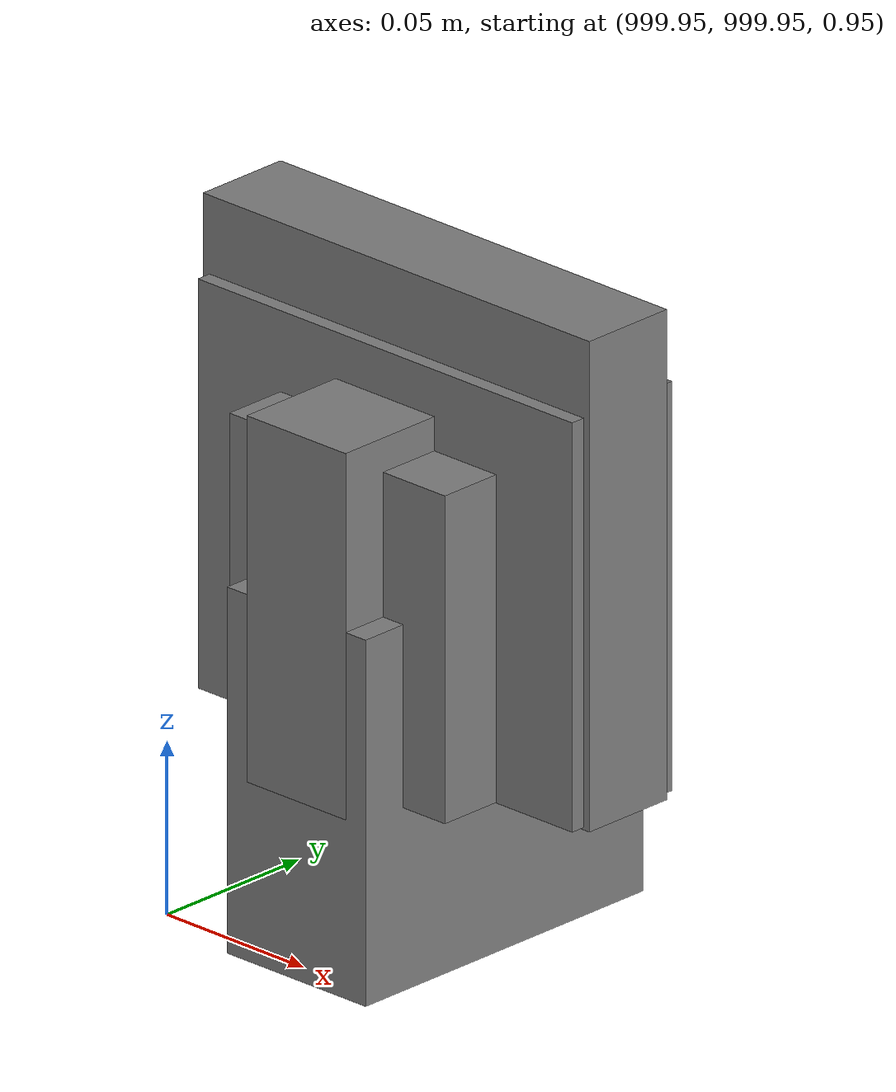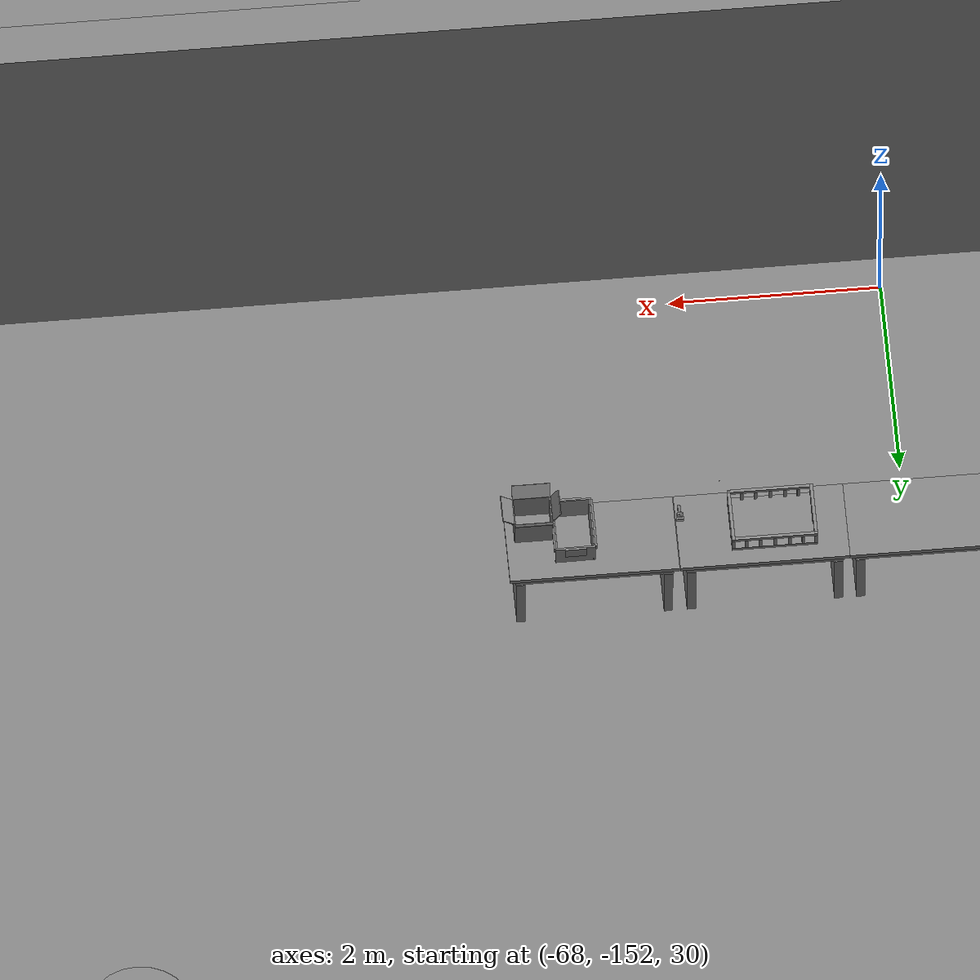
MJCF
<mujoco>
    <option gravity="0.000000000 0.000000000 -9.810000420" timestep="0.0049999999" integrator="implicitfast" density="1.225" viscosity="1.8000001e-05" noslip_iterations="10" iterations="100" sdf_iterations="50">
        <flag multiccd="disable"/>
    </option>
    <size memory="1000M"/>
    <compiler coordinate="local"/>
    <worldbody>
        <light cutoff="30" pos="0 1 1" dir="0 -1 -2"/>
        <light cutoff="30" pos="0 -1 1" dir="0 1 -2"/>
        <body pos="-64.866622925 -149.383972168 30.183746338" euler="89.999984741 89.999946594 0.000000000" name="openloong_gripper_2f85_fix_base_usda_bluebox_01">
            <geom contype="1" conaffinity="1" density="1000" type="box" material="" rgba="0.500000000 0.500000000 0.500000000 1.000000000" solimp="0.899999976 0.949999988 0.001000000" friction="1.000000000 0.005000000 0.000100000" solref="0.020000000 1.000000000" margin="0" condim="3" group="0" pos="0.276580811 0.187225342 0.000068665" quat="0.707106948 0.000077471 0.707106352 0.000077486" size="0.100000001 0.057999998 0.010000000" name="openloong_gripper_2f85_fix_base_usda_geom_8D5B2189_9BBD_420C_B04C_81A4645AFCCC"/>
            <geom contype="1" conaffinity="1" density="1000" type="box" material="" rgba="0.500000000 0.500000000 0.500000000 1.000000000" solimp="0.899999976 0.949999988 0.001000000" friction="1.000000000 0.005000000 0.000100000" solref="0.020000000 1.000000000" margin="0" condim="3" group="0" pos="0.000000000 0.002883911 0.000000000" quat="0.999999881 0.000000000 0.000000000 0.000000000" size="0.254000008 0.003000000 0.172000006" name="openloong_gripper_2f85_fix_base_usda_geom_8527D4AD_A886_4FC3_A9C4_77D04A640455"/>
            <geom contype="1" conaffinity="1" density="1000" type="box" material="" rgba="0.500000000 0.500000000 0.500000000 1.000000000" solimp="0.899999976 0.949999988 0.001000000" friction="1.000000000 0.005000000 0.000100000" solref="0.020000000 1.000000000" margin="0" condim="3" group="0" pos="0.000000000 0.124874115 0.173484802" quat="0.999796331 0.020176515 -0.000000015 0.000000030" size="0.259999990 0.119999997 0.007000000" name="openloong_gripper_2f85_fix_base_usda_geom_480853FE_5FD9_4062_ABCE_6E31790CF310"/>
            <geom contype="1" conaffinity="1" density="1000" type="box" material="" rgba="0.500000000 0.500000000 0.500000000 1.000000000" solimp="0.899999976 0.949999988 0.001000000" friction="1.000000000 0.005000000 0.000100000" solref="0.020000000 1.000000000" margin="0" condim="3" group="0" pos="0.000000000 0.124874115 -0.173469543" quat="0.999796331 -0.020176545 -0.000000015 0.000000000" size="0.259999990 0.119999997 0.007000000" name="openloong_gripper_2f85_fix_base_usda_geom_DBFFB196_20FF_42E6_873C_9178BB25B891"/>
            <geom contype="1" conaffinity="1" density="1000" type="box" material="" rgba="0.500000000 0.500000000 0.500000000 1.000000000" solimp="0.899999976 0.949999988 0.001000000" friction="1.000000000 0.005000000 0.000100000" solref="0.020000000 1.000000000" margin="0" condim="3" group="0" pos="0.000000000 0.214008331 0.188980103" quat="0.999912977 0.013176724 0.000000015 0.000000000" size="0.259999990 0.029999999 0.012500000" name="openloong_gripper_2f85_fix_base_usda_geom_E51F96EA_6F6A_49A5_A1BC_0EE5FC175241"/>
            <geom contype="1" conaffinity="1" density="1000" type="box" material="" rgba="0.500000000 0.500000000 0.500000000 1.000000000" solimp="0.899999976 0.949999988 0.001000000" friction="1.000000000 0.005000000 0.000100000" solref="0.020000000 1.000000000" margin="0" condim="3" group="0" pos="-0.258361816 0.125289917 0.001876831" quat="0.702796936 -0.020792112 0.710783124 0.020769298" size="0.189999998 0.119999997 0.009000000" name="openloong_gripper_2f85_fix_base_usda_geom_7CF74EB5_9935_47BF_8EB2_C477C35BED0B"/>
            <geom contype="1" conaffinity="1" density="1000" type="box" material="" rgba="0.500000000 0.500000000 0.500000000 1.000000000" solimp="0.899999976 0.949999988 0.001000000" friction="1.000000000 0.005000000 0.000100000" solref="0.020000000 1.000000000" margin="0" condim="3" group="0" pos="0.000000000 0.214008331 -0.188980103" quat="0.999912977 -0.013176769 0.000000030 0.000000015" size="0.259999990 0.029999999 0.012500000" name="openloong_gripper_2f85_fix_base_usda_geom_ACF1A779_A8AA_4C0F_AE44_46ED3584723F"/>
            <geom contype="1" conaffinity="1" density="1000" type="box" material="" rgba="0.500000000 0.500000000 0.500000000 1.000000000" solimp="0.899999976 0.949999988 0.001000000" friction="1.000000000 0.005000000 0.000100000" solref="0.020000000 1.000000000" margin="0" condim="3" group="0" pos="-0.276611328 0.187225342 0.000068665" quat="0.707106650 0.000077441 0.707106709 0.000077456" size="0.100000001 0.057999998 0.010000000" name="openloong_gripper_2f85_fix_base_usda_geom_6981F0F6_8BF4_4FAD_9FE8_ED3F4A247AD0"/>
            <geom contype="1" conaffinity="1" density="1000" type="box" material="" rgba="0.500000000 0.500000000 0.500000000 1.000000000" solimp="0.899999976 0.949999988 0.001000000" friction="1.000000000 0.005000000 0.000100000" solref="0.020000000 1.000000000" margin="0" condim="3" group="0" pos="0.258331299 0.125289917 0.001876831" quat="0.702851415 0.018856421 0.710823774 -0.019329369" size="0.189999998 0.119999997 0.009000000" name="openloong_gripper_2f85_fix_base_usda_geom_3F8CBD10_029A_419E_ADBF_B6322694FB53"/>
            <freejoint name="openloong_gripper_2f85_fix_base_usda_bluebox_01_joint"/>
            <site size="0.005000000 0.005000000 0.005000000" rgba="0.500000000 0.500000000 0.500000000 1.000000000" pos="0.000000000 0.000000000 0.000000000" quat="0.999961913 0.008726534 0.000000000 0.000000000" group="0" type="sphere" name="openloong_gripper_2f85_fix_base_usda_bluebox_01site"/>
        </body>
        <body pos="-64.496299744 -149.491867065 30.235729218" euler="0.000000000 0.000000000 89.999946594" name="openloong_gripper_2f85_fix_base_usda_cardboardbox_01">
            <geom contype="1" conaffinity="1" density="1000" type="box" material="" rgba="0.500000000 0.500000000 0.500000000 1.000000000" solimp="0.899999976 0.949999988 0.001000000" friction="1.000000000 0.005000000 0.000100000" solref="0.020000000 1.000000000" margin="0" condim="3" group="0" pos="-0.003166199 -0.004086494 0.005052090" quat="1.000000000 0.000000000 0.000000000 0.000000000" size="0.142499998 0.177500010 0.005000000" name="openloong_gripper_2f85_fix_base_usda_geom_7414F88F_F07C_44BB_BBAA_E78A21830AE6"/>
            <geom contype="1" conaffinity="1" density="1000" type="box" material="" rgba="0.500000000 0.500000000 0.500000000 1.000000000" solimp="0.899999976 0.949999988 0.001000000" friction="1.000000000 0.005000000 0.000100000" solref="0.020000000 1.000000000" margin="0" condim="3" group="0" pos="-0.003166199 0.170316696 0.150570869" quat="1.000000000 0.000000000 0.000000000 0.000000000" size="0.142499998 0.005000000 0.149999991" name="openloong_gripper_2f85_fix_base_usda_geom_63030FF6_C8DA_459F_AA56_C2EF70E58608"/>
            <geom contype="1" conaffinity="1" density="1000" type="box" material="" rgba="0.500000000 0.500000000 0.500000000 1.000000000" solimp="0.899999976 0.949999988 0.001000000" friction="1.000000000 0.005000000 0.000100000" solref="0.020000000 1.000000000" margin="0" condim="3" group="0" pos="-0.147399902 -0.005307198 0.150570869" quat="1.000000000 0.000000000 0.000000000 0.000000000" size="0.005000000 0.177500010 0.149999991" name="openloong_gripper_2f85_fix_base_usda_geom_CCF7B0FA_0298_44EF_A1AF_D0708869B9EC"/>
            <geom contype="1" conaffinity="1" density="1000" type="box" material="" rgba="0.500000000 0.500000000 0.500000000 1.000000000" solimp="0.899999976 0.949999988 0.001000000" friction="1.000000000 0.005000000 0.000100000" solref="0.020000000 1.000000000" margin="0" condim="3" group="0" pos="0.140275955 -0.005307198 0.150570869" quat="1.000000000 0.000000000 0.000000000 0.000000000" size="0.005000000 0.177500010 0.149999991" name="openloong_gripper_2f85_fix_base_usda_geom_BBE69D8B_2F10_4391_955D_7D6E65795DFF"/>
            <geom contype="1" conaffinity="1" density="1000" type="box" material="" rgba="0.500000000 0.500000000 0.500000000 1.000000000" solimp="0.899999976 0.949999988 0.001000000" friction="1.000000000 0.005000000 0.000100000" solref="0.020000000 1.000000000" margin="0" condim="3" group="0" pos="-0.003166199 -0.181550980 0.150570869" quat="1.000000000 0.000000000 0.000000000 0.000000000" size="0.142499998 0.005000000 0.149999991" name="openloong_gripper_2f85_fix_base_usda_geom_4E477AA1_69D4_49B5_AE45_AC257C53B070"/>
            <freejoint name="openloong_gripper_2f85_fix_base_usda_cardboardbox_01_joint"/>
            <site size="0.005000000 0.005000000 0.005000000" rgba="0.500000000 0.500000000 0.500000000 1.000000000" pos="0.000000000 0.000000000 0.000000000" quat="0.999961913 0.008726535 0.000000000 0.000000000" group="0" type="sphere" name="openloong_gripper_2f85_fix_base_usda_site_D06B8958_BD76_4E11_899F_368D678D7757"/>
            <body pos="0.139160156 -0.004048347 0.301930904" euler="-179.999954224 49.383502960 179.999954224" name="openloong_gripper_2f85_fix_base_usda_A1_006">
                <geom contype="1" conaffinity="1" density="1000" type="box" material="" rgba="0.500000000 0.500000000 0.500000000 1.000000000" solimp="0.899999976 0.949999988 0.001000000" friction="1.000000000 0.005000000 0.000100000" solref="0.020000000 1.000000000" margin="0" condim="3" group="0" pos="-0.071587563 0.000009537 0.001745224" quat="0.999999881 0.000000000 0.000000000 0.000000000" size="0.071249999 0.179999992 0.002500000" name="openloong_gripper_2f85_fix_base_usda_geom_F8209156_4994_4714_A722_7572CF8C3561"/>
                <joint armature="0" stiffness="0.07" damping="0.0099999998" axis="0.000000 1.000000 0.000000" type="hinge" name="openloong_gripper_2f85_fix_base_usda_A1_006"/>
            </body>
            <body pos="-0.145902634 -0.004086494 0.301938057" euler="-180.000000000 -60.000011444 -180.000000000" name="openloong_gripper_2f85_fix_base_usda_A2_006">
                <geom contype="1" conaffinity="1" density="1000" type="box" material="" rgba="0.500000000 0.500000000 0.500000000 1.000000000" solimp="0.899999976 0.949999988 0.001000000" friction="1.000000000 0.005000000 0.000100000" solref="0.020000000 1.000000000" margin="0" condim="3" group="0" pos="0.071268082 0.000009537 0.002717972" quat="0.000002921 0.000000000 -0.000000030 0.999999881" size="0.071249999 0.179999992 0.002500000" name="openloong_gripper_2f85_fix_base_usda_geom_EF4EAE5C_51EC_4E97_B701_D692361FFABD"/>
                <joint armature="0" stiffness="0.07" damping="0.0099999998" axis="0.000000 1.000000 0.000000" type="hinge" name="openloong_gripper_2f85_fix_base_usda_A2_006"/>
            </body>
            <body pos="-0.003385544 0.175991058 0.301930904" euler="-125.858116150 -0.000004561 0.000002331" name="openloong_gripper_2f85_fix_base_usda_B2_006">
                <geom contype="1" conaffinity="1" density="1000" type="box" material="" rgba="0.500000000 0.500000000 0.500000000 1.000000000" solimp="0.899999976 0.949999988 0.001000000" friction="1.000000000 0.005000000 0.000100000" solref="0.020000000 1.000000000" margin="0" condim="3" group="0" pos="0.000009537 -0.070939064 -0.002470016" quat="0.999614120 0.027776197 -0.000000015 0.000000030" size="0.137500003 0.064999998 0.005000000" name="openloong_gripper_2f85_fix_base_usda_geom_C4E0BBD1_B90A_4BC8_9E80_998ED2BFF663"/>
                <joint armature="0" stiffness="0.07" damping="0.0099999998" axis="1.000000 0.000000 0.000000" type="hinge" name="openloong_gripper_2f85_fix_base_usda_B2_006"/>
            </body>
            <body pos="-0.003385544 -0.184140205 0.301938057" euler="147.805557251 0.000000000 0.000000000" name="openloong_gripper_2f85_fix_base_usda_B1_006">
                <geom contype="1" conaffinity="1" density="1000" type="box" material="" rgba="0.500000000 0.500000000 0.500000000 1.000000000" solimp="0.899999976 0.949999988 0.001000000" friction="1.000000000 0.005000000 0.000100000" solref="0.020000000 1.000000000" margin="0" condim="3" group="0" pos="-0.000028610 0.070202351 -0.002703667" quat="0.999614179 -0.027776167 0.000000000 0.000000000" size="0.137500003 0.064999998 0.005000000" name="openloong_gripper_2f85_fix_base_usda_geom_ABAA93B2_44B5_4455_8174_EA90B180E91A"/>
                <joint armature="0" stiffness="0.07" damping="0.0099999998" axis="1.000000 0.000000 0.000000" type="hinge" name="openloong_gripper_2f85_fix_base_usda_B1_006"/>
            </body>
        </body>
        <body pos="-65.882858276 -149.481979370 30.229999542" euler="-64.487716675 0.000000000 0.000000000" name="openloong_gripper_2f85_fix_base_usda_Barcode">
            <geom contype="1" conaffinity="1" density="1000" type="box" material="" rgba="0.500000000 0.500000000 0.500000000 1.000000000" solimp="0.899999976 0.949999988 0.001000000" friction="1.000000000 0.005000000 0.000100000" solref="0.020000000 1.000000000" margin="0" condim="3" group="0" pos="0.000000000 0.013038635 0.001419067" quat="0.000000000 0.000000000 0.000000000 1.000000119" size="0.034000002 0.010000000 0.017999999" name="openloong_gripper_2f85_fix_base_usda_geom_4CA84FCE_E45F_4DF8_9E17_CA97AC39812C"/>
            <geom contype="1" conaffinity="1" density="1000" type="box" material="" rgba="0.500000000 0.500000000 0.500000000 1.000000000" solimp="0.899999976 0.949999988 0.001000000" friction="1.000000000 0.005000000 0.000100000" solref="0.020000000 1.000000000" margin="0" condim="3" group="0" pos="0.000000000 -0.035301208 -0.007095337" quat="0.000000000 0.000000000 -0.043619365 0.999048233" size="0.028999999 0.010000000 0.020000000" name="openloong_gripper_2f85_fix_base_usda_geom_5012F2CE_2438_45C8_876B_051AE2D435AA"/>
            <geom contype="1" conaffinity="1" density="1000" type="box" material="" rgba="0.500000000 0.500000000 0.500000000 1.000000000" solimp="0.899999976 0.949999988 0.001000000" friction="1.000000000 0.005000000 0.000100000" solref="0.020000000 1.000000000" margin="0" condim="3" group="0" pos="0.000000000 -0.043411255 -0.011749268" quat="0.922262907 0.386563420 0.000000000 0.000000000" size="0.026000001 0.010000000 0.020000000" name="openloong_gripper_2f85_fix_base_usda_geom_16622525_20B8_463E_966D_4D1423DC43B6"/>
            <geom contype="1" conaffinity="1" density="1000" type="box" material="" rgba="0.500000000 0.500000000 0.500000000 1.000000000" solimp="0.899999976 0.949999988 0.001000000" friction="1.000000000 0.005000000 0.000100000" solref="0.020000000 1.000000000" margin="0" condim="3" group="0" pos="0.000000000 -0.016967773 -0.031860352" quat="0.000000000 0.000000000 0.000000000 1.000000119" size="0.008000000 0.010000000 0.013000000" name="openloong_gripper_2f85_fix_base_usda_geom_3DDC626B_B155_47EB_8063_E42E3E54FB36"/>
            <geom contype="1" conaffinity="1" density="1000" type="box" material="" rgba="0.500000000 0.500000000 0.500000000 1.000000000" solimp="0.899999976 0.949999988 0.001000000" friction="1.000000000 0.005000000 0.000100000" solref="0.020000000 1.000000000" margin="0" condim="3" group="0" pos="0.000000000 -0.001869202 0.000312805" quat="0.953716993 0.300705761 0.000000000 0.000000000" size="0.032000002 0.010000000 0.018999999" name="openloong_gripper_2f85_fix_base_usda_geom_D0DAC7D1_018C_4E88_8459_2EFF051A1F8B"/>
            <geom contype="1" conaffinity="1" density="1000" type="box" material="" rgba="0.500000000 0.500000000 0.500000000 1.000000000" solimp="0.899999976 0.949999988 0.001000000" friction="1.000000000 0.005000000 0.000100000" solref="0.020000000 1.000000000" margin="0" condim="3" group="0" pos="0.000000000 -0.019531250 -0.003173828" quat="0.953716993 0.300705761 0.000000000 0.000000000" size="0.030999999 0.010000000 0.020000000" name="openloong_gripper_2f85_fix_base_usda_geom_53C26A4D_6580_4E05_888F_C75A578A49C2"/>
            <geom contype="1" conaffinity="1" density="1000" type="box" material="" rgba="0.500000000 0.500000000 0.500000000 1.000000000" solimp="0.899999976 0.949999988 0.001000000" friction="1.000000000 0.005000000 0.000100000" solref="0.020000000 1.000000000" margin="0" condim="3" group="0" pos="0.000000000 -0.035301208 -0.007095337" quat="0.953716993 0.300705761 0.000000000 0.000000000" size="0.028999999 0.010000000 0.020000000" name="openloong_gripper_2f85_fix_base_usda_geom_B9BB8E88_A2F5_46B5_BA9F_2BAFFD403725"/>
            <geom contype="1" conaffinity="1" density="1000" type="box" material="" rgba="0.500000000 0.500000000 0.500000000 1.000000000" solimp="0.899999976 0.949999988 0.001000000" friction="1.000000000 0.005000000 0.000100000" solref="0.020000000 1.000000000" margin="0" condim="3" group="0" pos="0.000000000 -0.042617798 -0.071121216" quat="0.000000000 0.000000000 0.000000000 1.000000119" size="0.013000000 0.021000000 0.059999999" name="openloong_gripper_2f85_fix_base_usda_geom_305A084F_5ABD_498E_8EC6_B02C5A333322"/>
            <freejoint name="openloong_gripper_2f85_fix_base_usda_Barcode_joint"/>
            <site size="0.005000000 0.005000000 0.005000000" rgba="0.500000000 0.500000000 0.500000000 1.000000000" pos="0.000000000 0.000000000 0.000000000" quat="1.000000000 0.000000000 0.000000000 0.000000000" group="0" type="sphere" name="openloong_gripper_2f85_fix_base_usda_Barcode_site"/>
        </body>
        <body pos="-66.745018005 -149.392349243 30.184000015" euler="0.000000000 0.000000000 89.999946594" name="[22330130869030]_Basket_01">
            <geom contype="1" conaffinity="1" density="1000" type="box" material="" rgba="0.500000000 0.500000000 0.500000000 1.000000000" solimp="0.899999976 0.949999988 0.001000000" friction="1.000000000 0.005000000 0.000100000" solref="0.020000000 1.000000000" margin="0" condim="3" group="0" pos="-0.052425385 0.389207840 0.089787483" quat="0.707107008 0.000000000 0.000000000 0.707106411" size="0.014249999 0.014249999 0.059999999" name="[22330130869030]_geom_9D717DA9_FFA8_41D1_99EE_0C8D096B9299"/>
            <geom contype="1" conaffinity="1" density="1000" type="box" material="" rgba="0.500000000 0.500000000 0.500000000 1.000000000" solimp="0.899999976 0.949999988 0.001000000" friction="1.000000000 0.005000000 0.000100000" solref="0.020000000 1.000000000" margin="0" condim="3" group="0" pos="0.264015198 -0.133043289 0.089787483" quat="0.707107008 0.000000000 0.000000000 0.707106411" size="0.014249999 0.014249999 0.059999999" name="[22330130869030]_geom_E5371305_FD69_4419_8616_50451DEF90DB"/>
            <geom contype="1" conaffinity="1" density="1000" type="box" material="" rgba="0.500000000 0.500000000 0.500000000 1.000000000" solimp="0.899999976 0.949999988 0.001000000" friction="1.000000000 0.005000000 0.000100000" solref="0.020000000 1.000000000" margin="0" condim="3" group="0" pos="-0.264015198 -0.265548706 0.089793205" quat="0.707107008 0.000000000 0.000000000 0.707106411" size="0.014249999 0.014249999 0.059999999" name="[22330130869030]_geom_1B34C2B1_567B_42B3_89A4_517B8A45B05D"/>
            <geom contype="1" conaffinity="1" density="1000" type="box" material="" rgba="0.500000000 0.500000000 0.500000000 1.000000000" solimp="0.899999976 0.949999988 0.001000000" friction="1.000000000 0.005000000 0.000100000" solref="0.020000000 1.000000000" margin="0" condim="3" group="0" pos="-0.160263062 -0.389322281 0.089793205" quat="0.707107008 0.000000000 0.000000000 0.707106411" size="0.014249999 0.014249999 0.059999999" name="[22330130869030]_geom_59774C11_6C8A_47B7_BE41_313B24E0210B"/>
            <geom contype="1" conaffinity="1" density="1000" type="box" material="" rgba="0.500000000 0.500000000 0.500000000 1.000000000" solimp="0.899999976 0.949999988 0.001000000" friction="1.000000000 0.005000000 0.000100000" solref="0.020000000 1.000000000" margin="0" condim="3" group="0" pos="0.162265778 -0.389322281 0.089787483" quat="0.707107008 0.000000000 0.000000000 0.707106411" size="0.014249999 0.014249999 0.059999999" name="[22330130869030]_geom_76399BF8_D090_496E_8AB1_7FD4DF1BE32A"/>
            <geom contype="1" conaffinity="1" density="1000" type="box" material="" rgba="0.500000000 0.500000000 0.500000000 1.000000000" solimp="0.899999976 0.949999988 0.001000000" friction="1.000000000 0.005000000 0.000100000" solref="0.020000000 1.000000000" margin="0" condim="3" group="0" pos="0.264015198 0.389207840 0.089787483" quat="0.707107008 0.000000000 0.000000000 0.707106411" size="0.014249999 0.014249999 0.059999999" name="[22330130869030]_geom_9CF3CCBE_4147_4427_8320_CBFAF8D3577F"/>
            <geom contype="1" conaffinity="1" density="1000" type="box" material="" rgba="0.500000000 0.500000000 0.500000000 1.000000000" solimp="0.899999976 0.949999988 0.001000000" friction="1.000000000 0.005000000 0.000100000" solref="0.020000000 1.000000000" margin="0" condim="3" group="0" pos="-0.264015198 -0.133043289 0.089793205" quat="0.707107008 0.000000000 0.000000000 0.707106411" size="0.014249999 0.014249999 0.059999999" name="[22330130869030]_geom_BD5A6ABF_D8BC_413A_8187_7E21F5E5B09B"/>
            <geom contype="1" conaffinity="1" density="1000" type="box" material="" rgba="0.500000000 0.500000000 0.500000000 1.000000000" solimp="0.899999976 0.949999988 0.001000000" friction="1.000000000 0.005000000 0.000100000" solref="0.020000000 1.000000000" margin="0" condim="3" group="0" pos="-0.264026642 0.269256592 0.089793205" quat="0.707107008 0.000000000 0.000000000 0.707106411" size="0.014249999 0.014249999 0.059999999" name="[22330130869030]_geom_89EAA85E_B499_4E3D_A65F_9B78F686C742"/>
            <geom contype="1" conaffinity="1" density="1000" type="box" material="" rgba="0.500000000 0.500000000 0.500000000 1.000000000" solimp="0.899999976 0.949999988 0.001000000" friction="1.000000000 0.005000000 0.000100000" solref="0.020000000 1.000000000" margin="0" condim="3" group="0" pos="0.054462433 0.389207840 0.089787483" quat="0.707107008 0.000000000 0.000000000 0.707106411" size="0.014249999 0.014249999 0.059999999" name="[22330130869030]_geom_04267315_9333_40CD_AF38_C0C02F2820C1"/>
            <geom contype="1" conaffinity="1" density="1000" type="box" material="" rgba="0.500000000 0.500000000 0.500000000 1.000000000" solimp="0.899999976 0.949999988 0.001000000" friction="1.000000000 0.005000000 0.000100000" solref="0.020000000 1.000000000" margin="0" condim="3" group="0" pos="0.054462433 -0.389322281 0.089787483" quat="0.707107008 0.000000000 0.000000000 0.707106411" size="0.014249999 0.014249999 0.059999999" name="[22330130869030]_geom_A531BE8C_DE77_4D33_8CC2_107289A943B1"/>
            <geom contype="1" conaffinity="1" density="1000" type="box" material="" rgba="0.500000000 0.500000000 0.500000000 1.000000000" solimp="0.899999976 0.949999988 0.001000000" friction="1.000000000 0.005000000 0.000100000" solref="0.020000000 1.000000000" margin="0" condim="3" group="0" pos="0.264015198 0.269256592 0.089793205" quat="0.707107008 0.000000000 0.000000000 0.707106411" size="0.014249999 0.014249999 0.059999999" name="[22330130869030]_geom_2B4A11A8_6879_47B9_A757_C6F02EEC719D"/>
            <geom contype="1" conaffinity="1" density="1000" type="box" material="" rgba="0.500000000 0.500000000 0.500000000 1.000000000" solimp="0.899999976 0.949999988 0.001000000" friction="1.000000000 0.005000000 0.000100000" solref="0.020000000 1.000000000" margin="0" condim="3" group="0" pos="0.264015198 -0.389322281 0.089787483" quat="0.707107008 0.000000000 0.000000000 0.707106411" size="0.014249999 0.014249999 0.059999999" name="[22330130869030]_geom_79D74BE4_C798_4DFE_BB27_2276B09D4DFC"/>
            <geom contype="1" conaffinity="1" density="1000" type="box" material="" rgba="0.500000000 0.500000000 0.500000000 1.000000000" solimp="0.899999976 0.949999988 0.001000000" friction="1.000000000 0.005000000 0.000100000" solref="0.020000000 1.000000000" margin="0" condim="3" group="0" pos="0.000000000 0.000000000 0.015998840" quat="0.707107008 0.000000000 0.000000000 0.707106411" size="0.403499991 0.279000014 0.015750000" name="[22330130869030]_geom_998A11FA_D4CB_48DD_9DEF_20AF39E7A4A0"/>
            <geom contype="1" conaffinity="1" density="1000" type="box" material="" rgba="0.500000000 0.500000000 0.500000000 1.000000000" solimp="0.899999976 0.949999988 0.001000000" friction="1.000000000 0.005000000 0.000100000" solref="0.020000000 1.000000000" margin="0" condim="3" group="0" pos="0.000000000 -0.389476776 0.163619041" quat="0.707107008 0.000000000 0.000000000 0.707106411" size="0.015000000 0.277500004 0.015750000" name="[22330130869030]_geom_03BF19F9_5810_4467_B999_201FB56033C7"/>
            <geom contype="1" conaffinity="1" density="1000" type="box" material="" rgba="0.500000000 0.500000000 0.500000000 1.000000000" solimp="0.899999976 0.949999988 0.001000000" friction="1.000000000 0.005000000 0.000100000" solref="0.020000000 1.000000000" margin="0" condim="3" group="0" pos="0.162265778 0.389207840 0.089787483" quat="0.707107008 0.000000000 0.000000000 0.707106411" size="0.014249999 0.014249999 0.059999999" name="[22330130869030]_geom_512478EF_E843_4204_8814_827F43E49533"/>
            <geom contype="1" conaffinity="1" density="1000" type="box" material="" rgba="0.500000000 0.500000000 0.500000000 1.000000000" solimp="0.899999976 0.949999988 0.001000000" friction="1.000000000 0.005000000 0.000100000" solref="0.020000000 1.000000000" margin="0" condim="3" group="0" pos="0.000000000 0.389471054 0.163619041" quat="0.707107008 0.000000000 0.000000000 0.707106411" size="0.015000000 0.277500004 0.015750000" name="[22330130869030]_geom_07A02709_9C1F_4491_8081_6E0A829512A4"/>
            <geom contype="1" conaffinity="1" density="1000" type="box" material="" rgba="0.500000000 0.500000000 0.500000000 1.000000000" solimp="0.899999976 0.949999988 0.001000000" friction="1.000000000 0.005000000 0.000100000" solref="0.020000000 1.000000000" margin="0" condim="3" group="0" pos="-0.263511658 0.000000000 0.163619041" quat="0.707107008 0.000000000 0.000000000 0.707106411" size="0.403499991 0.015000000 0.015750000" name="[22330130869030]_geom_CA84BAEF_2DFB_4F93_B43A_728826CE3864"/>
            <geom contype="1" conaffinity="1" density="1000" type="box" material="" rgba="0.500000000 0.500000000 0.500000000 1.000000000" solimp="0.899999976 0.949999988 0.001000000" friction="1.000000000 0.005000000 0.000100000" solref="0.020000000 1.000000000" margin="0" condim="3" group="0" pos="-0.264015198 0.141334534 0.089793205" quat="0.707107008 0.000000000 0.000000000 0.707106411" size="0.014249999 0.014249999 0.059999999" name="[22330130869030]_geom_FDF710F0_EFC1_4629_8459_5CED1134810D"/>
            <geom contype="1" conaffinity="1" density="1000" type="box" material="" rgba="0.500000000 0.500000000 0.500000000 1.000000000" solimp="0.899999976 0.949999988 0.001000000" friction="1.000000000 0.005000000 0.000100000" solref="0.020000000 1.000000000" margin="0" condim="3" group="0" pos="0.264015198 -0.265548706 0.089787483" quat="0.707107008 0.000000000 0.000000000 0.707106411" size="0.014249999 0.014249999 0.059999999" name="[22330130869030]_geom_05373621_3090_465F_9CD9_E12D71AEA46B"/>
            <geom contype="1" conaffinity="1" density="1000" type="box" material="" rgba="0.500000000 0.500000000 0.500000000 1.000000000" solimp="0.899999976 0.949999988 0.001000000" friction="1.000000000 0.005000000 0.000100000" solref="0.020000000 1.000000000" margin="0" condim="3" group="0" pos="-0.160263062 0.389207840 0.089787483" quat="0.707107008 0.000000000 0.000000000 0.707106411" size="0.014249999 0.014249999 0.059999999" name="[22330130869030]_geom_EB6674FE_E23E_4850_A65B_BADD86AF083C"/>
            <geom contype="1" conaffinity="1" density="1000" type="box" material="" rgba="0.500000000 0.500000000 0.500000000 1.000000000" solimp="0.899999976 0.949999988 0.001000000" friction="1.000000000 0.005000000 0.000100000" solref="0.020000000 1.000000000" margin="0" condim="3" group="0" pos="-0.052425385 -0.389322281 0.089787483" quat="0.707107008 0.000000000 0.000000000 0.707106411" size="0.014249999 0.014249999 0.059999999" name="[22330130869030]_geom_3E39C6F8_595C_4EAD_BE10_D4DFA85348AC"/>
            <geom contype="1" conaffinity="1" density="1000" type="box" material="" rgba="0.500000000 0.500000000 0.500000000 1.000000000" solimp="0.899999976 0.949999988 0.001000000" friction="1.000000000 0.005000000 0.000100000" solref="0.020000000 1.000000000" margin="0" condim="3" group="0" pos="-0.264026642 -0.389322281 0.089793205" quat="0.707107008 0.000000000 0.000000000 0.707106411" size="0.014249999 0.014249999 0.059999999" name="[22330130869030]_geom_6FABCA0B_2854_491C_83E6_07758596BD50"/>
            <geom contype="1" conaffinity="1" density="1000" type="box" material="" rgba="0.500000000 0.500000000 0.500000000 1.000000000" solimp="0.899999976 0.949999988 0.001000000" friction="1.000000000 0.005000000 0.000100000" solref="0.020000000 1.000000000" margin="0" condim="3" group="0" pos="0.264015198 0.141334534 0.089787483" quat="0.707107008 0.000000000 0.000000000 0.707106411" size="0.014249999 0.014249999 0.059999999" name="[22330130869030]_geom_715A4BD4_4FF6_4E15_944A_22E82C60BB11"/>
            <geom contype="1" conaffinity="1" density="1000" type="box" material="" rgba="0.500000000 0.500000000 0.500000000 1.000000000" solimp="0.899999976 0.949999988 0.001000000" friction="1.000000000 0.005000000 0.000100000" solref="0.020000000 1.000000000" margin="0" condim="3" group="0" pos="-0.264015198 0.389207840 0.089793205" quat="0.707107008 0.000000000 0.000000000 0.707106411" size="0.014249999 0.014249999 0.059999999" name="[22330130869030]_geom_CFCC47F7_AA39_4E1A_93E8_A046EB6C3EE4"/>
            <geom contype="1" conaffinity="1" density="1000" type="box" material="" rgba="0.500000000 0.500000000 0.500000000 1.000000000" solimp="0.899999976 0.949999988 0.001000000" friction="1.000000000 0.005000000 0.000100000" solref="0.020000000 1.000000000" margin="0" condim="3" group="0" pos="0.264015198 0.004480362 0.089787483" quat="0.707107008 0.000000000 0.000000000 0.707106411" size="0.014249999 0.014249999 0.059999999" name="[22330130869030]_geom_C71D62DF_A1C8_439E_9A78_94D56FCB5327"/>
            <geom contype="1" conaffinity="1" density="1000" type="box" material="" rgba="0.500000000 0.500000000 0.500000000 1.000000000" solimp="0.899999976 0.949999988 0.001000000" friction="1.000000000 0.005000000 0.000100000" solref="0.020000000 1.000000000" margin="0" condim="3" group="0" pos="0.263694763 -0.000011444 0.163619041" quat="0.707107008 0.000000000 0.000000000 0.707106411" size="0.403499991 0.015000000 0.015750000" name="[22330130869030]_geom_8DF56E45_FEB9_42B3_A232_C1609369932B"/>
            <geom contype="1" conaffinity="1" density="1000" type="box" material="" rgba="0.500000000 0.500000000 0.500000000 1.000000000" solimp="0.899999976 0.949999988 0.001000000" friction="1.000000000 0.005000000 0.000100000" solref="0.020000000 1.000000000" margin="0" condim="3" group="0" pos="-0.264015198 0.004480362 0.089793205" quat="0.707107008 0.000000000 0.000000000 0.707106411" size="0.014249999 0.014249999 0.059999999" name="[22330130869030]_geom_342447BF_7096_4E17_B3F6_8536C909E7EE"/>
            <freejoint name="[22330130869030]_joint_B7A180CF_AA3C_4C89_9613_54D1CEFDD536"/>
        </body>
        <body pos="0.000000000 0.000000000 0.000000000" euler="0.000000000 0.000000000 0.000000000" name="Static Objects_Static Objects">
            <geom contype="1" conaffinity="1" density="1000" type="box" material="" rgba="0.500000000 0.500000000 0.500000000 1.000000000" solimp="0.899999976 0.949999988 0.001000000" friction="1.000000000 0.005000000 0.000100000" solref="0.020000000 1.000000000" margin="0" condim="3" group="0" pos="-67.544113159 -149.365814209 29.727830887" quat="0.500000417 0.499999970 0.499999553 0.499999970" size="0.381000012 0.319999993 0.041000001" name="Static Objects_geom_C7F7CE75_2DF6_4B6C_8C50_0093214C72A2"/>
            <geom contype="1" conaffinity="1" density="1000" type="box" material="" rgba="0.500000000 0.500000000 0.500000000 1.000000000" solimp="0.899999976 0.949999988 0.001000000" friction="1.000000000 0.005000000 0.000100000" solref="0.020000000 1.000000000" margin="0" condim="3" group="0" pos="-68.239501953 -149.365814209 30.086868286" quat="0.500000417 0.499999970 0.499999553 0.499999970" size="0.370999992 0.039500002 0.745000005" name="Static Objects_geom_D885B369_7E95_45EF_B951_3D1B5AFC38C4"/>
            <geom contype="1" conaffinity="1" density="1000" type="box" material="" rgba="0.500000000 0.500000000 0.500000000 1.000000000" solimp="0.899999976 0.949999988 0.001000000" friction="1.000000000 0.005000000 0.000100000" solref="0.020000000 1.000000000" margin="0" condim="3" group="0" pos="-68.239501953 -149.365814209 30.147235870" quat="0.500000417 0.499999970 0.499999553 0.499999970" size="0.400000006 0.022000000 0.800000012" name="Static Objects_geom_4B6F4F1D_30E4_4B1A_954F_4F3F7C921F25"/>
            <geom contype="1" conaffinity="1" density="1000" type="box" material="" rgba="0.500000000 0.500000000 0.500000000 1.000000000" solimp="0.899999976 0.949999988 0.001000000" friction="1.000000000 0.005000000 0.000100000" solref="0.020000000 1.000000000" margin="0" condim="3" group="0" pos="-68.934890747 -149.365814209 29.727830887" quat="0.500000417 0.499999970 0.499999553 0.499999970" size="0.381000012 0.319999993 0.041000001" name="Static Objects_geom_D08EF747_C9DA_4D71_9673_DBDF7380E2FF"/>
            <geom contype="1" conaffinity="1" density="1000" type="box" material="" rgba="0.500000000 0.500000000 0.500000000 1.000000000" solimp="0.899999976 0.949999988 0.001000000" friction="1.000000000 0.005000000 0.000100000" solref="0.020000000 1.000000000" margin="0" condim="3" group="0" pos="-68.239501953 -149.365814209 29.561563492" quat="0.500000417 0.499999970 0.499999553 0.499999970" size="0.020000000 0.022000000 0.660000026" name="Static Objects_geom_AF2E360D_3A98_40AD_9623_AE1FA8D46DF1"/>
            <geom contype="1" conaffinity="1" density="1000" type="box" material="" rgba="0.500000000 0.500000000 0.500000000 1.000000000" solimp="0.899999976 0.949999988 0.001000000" friction="1.000000000 0.005000000 0.000100000" solref="0.020000000 1.000000000" margin="0" condim="3" group="0" pos="-65.945671082 -149.365814209 29.727830887" quat="0.500000417 0.499999970 0.499999553 0.499999970" size="0.381000012 0.319999993 0.041000001" name="Static Objects_geom_81BD8025_1EE9_4E6C_8103_08FADA7322A5"/>
            <geom contype="1" conaffinity="1" density="1000" type="box" material="" rgba="0.500000000 0.500000000 0.500000000 1.000000000" solimp="0.899999976 0.949999988 0.001000000" friction="1.000000000 0.005000000 0.000100000" solref="0.020000000 1.000000000" margin="0" condim="3" group="0" pos="-66.641059875 -149.365814209 30.086868286" quat="0.500000417 0.499999970 0.499999553 0.499999970" size="0.370999992 0.039500002 0.745000005" name="Static Objects_geom_9E6C1C64_90E8_4128_B83A_A1B90625E5EF"/>
            <geom contype="1" conaffinity="1" density="1000" type="box" material="" rgba="0.500000000 0.500000000 0.500000000 1.000000000" solimp="0.899999976 0.949999988 0.001000000" friction="1.000000000 0.005000000 0.000100000" solref="0.020000000 1.000000000" margin="0" condim="3" group="0" pos="-66.641059875 -149.365814209 30.147235870" quat="0.500000417 0.499999970 0.499999553 0.499999970" size="0.400000006 0.022000000 0.800000012" name="Static Objects_geom_C2279914_8477_4C83_A996_F8297B98B4BC"/>
            <geom contype="1" conaffinity="1" density="1000" type="box" material="" rgba="0.500000000 0.500000000 0.500000000 1.000000000" solimp="0.899999976 0.949999988 0.001000000" friction="1.000000000 0.005000000 0.000100000" solref="0.020000000 1.000000000" margin="0" condim="3" group="0" pos="-67.336448669 -149.365814209 29.727830887" quat="0.500000417 0.499999970 0.499999553 0.499999970" size="0.381000012 0.319999993 0.041000001" name="Static Objects_geom_0F77AECA_B66C_4583_867B_31DFBA47E912"/>
            <geom contype="1" conaffinity="1" density="1000" type="box" material="" rgba="0.500000000 0.500000000 0.500000000 1.000000000" solimp="0.899999976 0.949999988 0.001000000" friction="1.000000000 0.005000000 0.000100000" solref="0.020000000 1.000000000" margin="0" condim="3" group="0" pos="-66.641059875 -149.365814209 29.561563492" quat="0.500000417 0.499999970 0.499999553 0.499999970" size="0.020000000 0.022000000 0.660000026" name="Static Objects_geom_0AB16BE0_4BE4_4245_A413_88BADF155FF6"/>
            <geom contype="1" conaffinity="1" density="1000" type="box" material="" rgba="0.500000000 0.500000000 0.500000000 1.000000000" solimp="0.899999976 0.949999988 0.001000000" friction="1.000000000 0.005000000 0.000100000" solref="0.020000000 1.000000000" margin="0" condim="3" group="0" pos="-64.338577271 -149.365814209 29.727830887" quat="0.500000417 0.499999970 0.499999553 0.499999970" size="0.381000012 0.319999993 0.041000001" name="Static Objects_geom_C164F660_231C_4AC8_9B6C_B8001374EB24"/>
            <geom contype="1" conaffinity="1" density="1000" type="box" material="" rgba="0.500000000 0.500000000 0.500000000 1.000000000" solimp="0.899999976 0.949999988 0.001000000" friction="1.000000000 0.005000000 0.000100000" solref="0.020000000 1.000000000" margin="0" condim="3" group="0" pos="-65.033966064 -149.365814209 30.086868286" quat="0.500000417 0.499999970 0.499999553 0.499999970" size="0.370999992 0.039500002 0.745000005" name="Static Objects_geom_0813881B_5DF7_4B9F_9867_A2701D278840"/>
            <geom contype="1" conaffinity="1" density="1000" type="box" material="" rgba="0.500000000 0.500000000 0.500000000 1.000000000" solimp="0.899999976 0.949999988 0.001000000" friction="1.000000000 0.005000000 0.000100000" solref="0.020000000 1.000000000" margin="0" condim="3" group="0" pos="-65.033966064 -149.365814209 30.147235870" quat="0.500000417 0.499999970 0.499999553 0.499999970" size="0.400000006 0.022000000 0.800000012" name="Static Objects_geom_728AA832_4D0E_4492_B28B_DFA57A0075C4"/>
            <geom contype="1" conaffinity="1" density="1000" type="box" material="" rgba="0.500000000 0.500000000 0.500000000 1.000000000" solimp="0.899999976 0.949999988 0.001000000" friction="1.000000000 0.005000000 0.000100000" solref="0.020000000 1.000000000" margin="0" condim="3" group="0" pos="-65.729354858 -149.365814209 29.727830887" quat="0.500000417 0.499999970 0.499999553 0.499999970" size="0.381000012 0.319999993 0.041000001" name="Static Objects_geom_9F4BEE1D_C5CD_486D_A475_4542876CA9F7"/>
            <geom contype="1" conaffinity="1" density="1000" type="box" material="" rgba="0.500000000 0.500000000 0.500000000 1.000000000" solimp="0.899999976 0.949999988 0.001000000" friction="1.000000000 0.005000000 0.000100000" solref="0.020000000 1.000000000" margin="0" condim="3" group="0" pos="-65.033966064 -149.365814209 29.561563492" quat="0.500000417 0.499999970 0.499999553 0.499999970" size="0.020000000 0.022000000 0.660000026" name="Static Objects_geom_9C519321_7D8B_4A21_A32D_5132804B9FD2"/>
            <geom contype="1" conaffinity="1" density="1000" type="box" material="" rgba="0.500000000 0.500000000 0.500000000 1.000000000" solimp="0.899999976 0.949999988 0.001000000" friction="1.000000000 0.005000000 0.000100000" solref="0.020000000 1.000000000" margin="0" condim="3" group="0" pos="-61.754566193 -137.853729248 33.906845093" quat="0.707107067 0.000000000 0.000000000 0.707106471" size="0.759999990 0.759999990 4.500000000" name="Static Objects_geom_389D99C5_35C7_4E10_A932_E66F08217C37"/>
            <geom contype="1" conaffinity="1" density="1000" type="box" material="" rgba="0.500000000 0.500000000 0.500000000 1.000000000" solimp="0.899999976 0.949999988 0.001000000" friction="1.000000000 0.005000000 0.000100000" solref="0.020000000 1.000000000" margin="0" condim="3" group="0" pos="-57.511135101 -144.927108765 31.707921982" quat="1.000000000 0.000000000 0.000000000 0.000000000" size="0.200000003 8.000000000 2.299999952" name="Static Objects_geom_441616DD_EE07_4394_97A4_69C05EC1A4C2"/>
            <geom contype="1" conaffinity="1" density="1000" type="box" material="" rgba="0.500000000 0.500000000 0.500000000 1.000000000" solimp="0.899999976 0.949999988 0.001000000" friction="1.000000000 0.005000000 0.000100000" solref="0.020000000 1.000000000" margin="0" condim="3" group="0" pos="-80.517646790 -157.574050903 31.688196182" quat="0.707107067 0.000000000 0.000000000 0.707106471" size="0.600000024 0.600000024 2.299999952" name="Static Objects_geom_9E8FBE48_2C04_4BD1_9104_F10D78E1FE15"/>
            <geom contype="1" conaffinity="1" density="1000" type="box" material="" rgba="0.500000000 0.500000000 0.500000000 1.000000000" solimp="0.899999976 0.949999988 0.001000000" friction="1.000000000 0.005000000 0.000100000" solref="0.020000000 1.000000000" margin="0" condim="3" group="0" pos="-80.711044312 -147.414932251 31.666158676" quat="1.000000000 0.000000000 0.000000000 0.000000000" size="0.200000003 10.000000000 2.299999952" name="Static Objects_geom_3FBAE04D_6195_48B2_9FA0_34D3A792EF2D"/>
            <geom contype="1" conaffinity="1" density="1000" type="box" material="" rgba="0.500000000 0.500000000 0.500000000 1.000000000" solimp="0.899999976 0.949999988 0.001000000" friction="1.000000000 0.005000000 0.000100000" solref="0.020000000 1.000000000" margin="0" condim="3" group="0" pos="-57.687217712 -137.434692383 31.688196182" quat="0.707107067 0.000000000 0.000000000 0.707106471" size="0.600000024 0.600000024 2.299999952" name="Static Objects_geom_BAC3A2FD_7515_46FF_8DFB_1FFEC28D1327"/>
            <geom contype="1" conaffinity="1" density="1000" type="box" material="" rgba="0.500000000 0.500000000 0.500000000 1.000000000" solimp="0.899999976 0.949999988 0.001000000" friction="1.000000000 0.005000000 0.000100000" solref="0.020000000 1.000000000" margin="0" condim="3" group="0" pos="-69.537033081 -140.263229370 31.714921951" quat="0.707107067 0.000000000 0.000000000 0.707106471" size="0.759999990 4.500000000 2.299999952" name="Static Objects_geom_562D7911_E99F_4ACD_B422_1A8F3F5613B4"/>
            <geom contype="1" conaffinity="1" density="1000" type="box" material="" rgba="0.500000000 0.500000000 0.500000000 1.000000000" solimp="0.899999976 0.949999988 0.001000000" friction="1.000000000 0.005000000 0.000100000" solref="0.020000000 1.000000000" margin="0" condim="3" group="0" pos="-80.073638916 -137.853713989 33.906845093" quat="0.707107067 0.000000000 0.000000000 0.707106471" size="0.759999990 0.759999990 4.500000000" name="Static Objects_geom_A458448F_65DB_4BA7_B471_9E37887239FF"/>
            <geom contype="1" conaffinity="1" density="1000" type="box" material="" rgba="0.500000000 0.500000000 0.500000000 1.000000000" solimp="0.899999976 0.949999988 0.001000000" friction="1.000000000 0.005000000 0.000100000" solref="0.020000000 1.000000000" margin="0" condim="3" group="0" pos="-73.406707764 -155.734664917 31.707921982" quat="1.000000000 0.000000000 0.000000000 0.000000000" size="0.200000003 3.000000000 2.299999952" name="Static Objects_geom_8A591304_010B_494F_B068_D00C9DDFA0EF"/>
            <geom contype="1" conaffinity="1" density="1000" type="box" material="" rgba="0.500000000 0.500000000 0.500000000 1.000000000" solimp="0.899999976 0.949999988 0.001000000" friction="1.000000000 0.005000000 0.000100000" solref="0.020000000 1.000000000" margin="0" condim="3" group="0" pos="-68.497543335 -137.448257446 31.707921982" quat="0.707107067 0.000000000 0.000000000 0.707106471" size="0.200000003 14.000000000 2.299999952" name="Static Objects_geom_28CC8986_9730_4923_A530_60CF7F56AD54"/>
            <geom contype="1" conaffinity="1" density="1000" type="cylinder" material="" rgba="0.500000000 0.500000000 0.500000000 1.000000000" solimp="0.899999976 0.949999988 0.001000000" friction="1.000000000 0.005000000 0.000100000" solref="0.020000000 1.000000000" margin="0" condim="3" group="0" pos="-68.868522644 -142.134506226 31.711090088" quat="0.707107067 0.000000000 0.000000000 0.707106471" size="0.509999990 2.299999952 1.000000000" name="Static Objects_geom_5D9ED61A_DA83_4B29_BA76_0FA758F35135"/>
            <geom contype="1" conaffinity="1" density="1000" type="plane" material="" rgba="0.500000000 0.500000000 0.500000000 1.000000000" solimp="0.899999976 0.949999988 0.001000000" friction="1.000000000 0.005000000 0.000100000" solref="0.020000000 1.000000000" margin="0" condim="3" group="0" pos="-72.873703003 -147.131927490 29.409669876" quat="1.000000000 0.000000000 0.000000000 0.000000000" size="18.000000000 14.000000000 1.000000000" name="Static Objects_geom_E21142F3_54FD_4D96_8AE8_72E18F024747"/>
            <geom contype="1" conaffinity="1" density="1000" type="box" material="" rgba="0.500000000 0.500000000 0.500000000 1.000000000" solimp="0.899999976 0.949999988 0.001000000" friction="1.000000000 0.005000000 0.000100000" solref="0.020000000 1.000000000" margin="0" condim="3" group="0" pos="-79.943580627 -157.782272339 31.707921982" quat="0.707107067 0.000000000 0.000000000 0.707106471" size="0.200000003 7.000000000 2.299999952" name="Static Objects_geom_087E9AE9_5A06_4E6E_9126_EF0B6EE4ECCB"/>
            <geom contype="1" conaffinity="1" density="1000" type="box" material="" rgba="0.500000000 0.500000000 0.500000000 1.000000000" solimp="0.899999976 0.949999988 0.001000000" friction="1.000000000 0.005000000 0.000100000" solref="0.020000000 1.000000000" margin="0" condim="3" group="0" pos="-65.421028137 -152.903442383 31.707921982" quat="0.707107067 0.000000000 0.000000000 0.707106471" size="0.200000003 7.800000191 2.299999952" name="Static Objects_geom_370396BF_A3B6_4A16_B654_87D02670534D"/>
            <geom contype="1" conaffinity="1" density="1000" type="box" material="" rgba="0.500000000 0.500000000 0.500000000 1.000000000" solimp="0.899999976 0.949999988 0.001000000" friction="1.000000000 0.005000000 0.000100000" solref="0.020000000 1.000000000" margin="0" condim="3" group="0" pos="-74.776908875 -149.964416504 31.688196182" quat="1.000000000 0.000000000 0.000000000 0.000000000" size="0.600000024 0.409999996 2.299999952" name="Static Objects_geom_EB2291AF_B027_4219_8775_6C747DE25990"/>
            <geom contype="1" conaffinity="1" density="1000" type="cylinder" material="" rgba="0.500000000 0.500000000 0.500000000 1.000000000" solimp="0.899999976 0.949999988 0.001000000" friction="1.000000000 0.005000000 0.000100000" solref="0.020000000 1.000000000" margin="0" condim="3" group="0" pos="-60.161884308 -142.134506226 31.711090088" quat="0.707107067 0.000000000 0.000000000 0.707106471" size="0.509999990 2.299999952 1.000000000" name="Static Objects_geom_C5D2FB6E_620E_4D3F_AB20_0376EFC6B108"/>
            <geom contype="1" conaffinity="1" density="1000" type="cylinder" material="" rgba="0.500000000 0.500000000 0.500000000 1.000000000" solimp="0.899999976 0.949999988 0.001000000" friction="1.000000000 0.005000000 0.000100000" solref="0.020000000 1.000000000" margin="0" condim="3" group="0" pos="-75.382453918 -149.963455200 31.711090088" quat="0.707107067 0.000000000 0.000000000 0.707106471" size="0.409999996 2.299999952 1.000000000" name="Static Objects_geom_0035C743_9960_477A_A3C0_CD66BEE13F80"/>
            <geom contype="1" conaffinity="1" density="1000" type="cylinder" material="" rgba="0.500000000 0.500000000 0.500000000 1.000000000" solimp="0.899999976 0.949999988 0.001000000" friction="1.000000000 0.005000000 0.000100000" solref="0.020000000 1.000000000" margin="0" condim="3" group="0" pos="-74.154960632 -149.963455200 31.711090088" quat="0.707107067 0.000000000 0.000000000 0.707106471" size="0.409999996 2.299999952 1.000000000" name="Static Objects_geom_FD0D9FDF_8580_483F_AB2F_DD03480F7676"/>
            <geom contype="1" conaffinity="1" density="1000" type="cylinder" material="" rgba="0.500000000 0.500000000 0.500000000 1.000000000" solimp="0.899999976 0.949999988 0.001000000" friction="1.000000000 0.005000000 0.000100000" solref="0.020000000 1.000000000" margin="0" condim="3" group="0" pos="-77.566612244 -142.134506226 31.711090088" quat="0.707107067 0.000000000 0.000000000 0.707106471" size="0.509999990 2.299999952 1.000000000" name="Static Objects_geom_5F9743E2_0397_4141_BD71_8D86E7D44A47"/>
        </body>
        <body pos="1000.000000000 1000.000000000 1.000000000" euler="0.000000000 0.000000000 180.000000000" name="openloong_gripper_2f85_fix_base_usda_cpu_fan">
            <geom contype="1" conaffinity="1" density="1000" type="box" material="" rgba="0.500000000 0.500000000 0.500000000 1.000000000" solimp="0.899999976 0.949999988 0.001000000" friction="1.000000000 0.005000000 0.000100000" solref="0.020000000 1.000000000" margin="0" condim="3" group="0" pos="0.000000000 0.000000000 0.070034981" quat="0.000000000 0.000000000 0.000000000 1.000000000" size="0.070700005 0.014699999 0.070700005" name="openloong_gripper_2f85_fix_base_usda_geom_91A4F6F9_2122_49BC_AC91_5DA61FF42068"/>
            <freejoint name="openloong_gripper_2f85_fix_base_usda_cpu_fan_joint"/>
            <site size="0.005000000 0.005000000 0.005000000" rgba="0.500000000 0.500000000 0.500000000 1.000000000" pos="0.000000000 0.000000000 0.000000000" quat="0.999961913 0.008726535 0.000000000 0.000000000" group="0" type="sphere" name="openloong_gripper_2f85_fix_base_usda_cpu_fancsite"/>
        </body>
        <body pos="1000.000000000 1000.000000000 1.000000000" euler="0.000011953 0.000005123 -179.999984741" name="openloong_gripper_2f85_fix_base_usda_intel_box">
            <geom contype="1" conaffinity="1" density="1000" type="box" material="" rgba="0.500000000 0.500000000 0.500000000 1.000000000" solimp="0.899999976 0.949999988 0.001000000" friction="1.000000000 0.005000000 0.000100000" solref="0.020000000 1.000000000" margin="0" condim="3" group="0" pos="0.000000000 -0.000067139 0.000082284" quat="0.707106709 0.000000225 0.000000253 0.707106650" size="0.052800003 0.025300000 0.052800003" name="openloong_gripper_2f85_fix_base_usda_geom_9D219FEF_32A0_43E1_AC4A_9FA2A6BCE5C0"/>
            <freejoint name="openloong_gripper_2f85_fix_base_usda_intel_box_joint"/>
            <site size="0.005000000 0.005000000 0.005000000" rgba="0.500000000 0.500000000 0.500000000 1.000000000" pos="0.000000000 0.000000000 0.000000000" quat="0.999961913 0.008726500 0.000000000 0.000000000" group="0" type="sphere" name="openloong_gripper_2f85_fix_base_usda_intel_boxsite"/>
        </body>
        <body pos="-66.239814758 -149.728012085 31.166406631" euler="-70.783622742 -63.915451050 93.974029541" mocap="true" name="spotlight5_SpotLight"/>
        <body pos="1000.000000000 999.999938965 1.000000000" euler="0.000000000 0.000000000 180.000000000" name="openloong_gripper_2f85_fix_base_usda_intelcore_i5">
            <geom contype="1" conaffinity="1" density="1000" type="box" material="" rgba="0.500000000 0.500000000 0.500000000 1.000000000" solimp="0.899999976 0.949999988 0.001000000" friction="1.000000000 0.005000000 0.000100000" solref="0.020000000 1.000000000" margin="0" condim="3" group="0" pos="0.000000000 0.000000000 0.051722717" quat="0.707106709 0.000000000 0.000000000 -0.707106769" size="0.052800000 0.018080002 0.052800000" name="openloong_gripper_2f85_fix_base_usda_geom_65A950AF_D484_48CB_B8CA_762CEE0E8F52"/>
            <freejoint name="openloong_gripper_2f85_fix_base_usda_intelcore_i5_joint"/>
            <site size="0.005000000 0.005000000 0.005000000" rgba="0.500000000 0.500000000 0.500000000 1.000000000" pos="0.000000000 0.000000000 0.000000000" quat="0.999961913 0.008726534 0.000000000 0.000000000" group="0" type="sphere" name="openloong_gripper_2f85_fix_base_usda_intelcore_i5site"/>
        </body>
        <body pos="1000.000000000 1000.000000000 1.000000000" euler="0.000000000 0.000000000 180.000000000" name="openloong_gripper_2f85_fix_base_usda_wifi_box">
            <geom contype="1" conaffinity="1" density="1000" type="box" material="" rgba="0.500000000 0.500000000 0.500000000 1.000000000" solimp="0.899999976 0.949999988 0.001000000" friction="1.000000000 0.005000000 0.000100000" solref="0.020000000 1.000000000" margin="0" condim="3" group="0" pos="0.000000000 0.000000000 0.058978677" quat="0.000000000 0.000000047 0.000000000 1.000000000" size="0.068499997 0.018999999 0.059000000" name="openloong_gripper_2f85_fix_base_usda_geom_C2C47550_9FCC_4533_97A4_854536CEB416"/>
            <freejoint name="openloong_gripper_2f85_fix_base_usda_wifi_box_joint"/>
            <site size="0.005000000 0.005000000 0.005000000" rgba="0.500000000 0.500000000 0.500000000 1.000000000" pos="0.000000000 0.000000000 0.000000000" quat="0.999961913 0.008726500 0.000000000 0.000000000" group="0" type="sphere" name="openloong_gripper_2f85_fix_base_usda_wifi_boxsite"/>
        </body>
        <body pos="-66.108764648 -149.394378662 31.163534164" euler="-49.106330872 80.457618713 -8.255789757" mocap="true" name="spotlight1_SpotLight"/>
        <body pos="-65.882675171 -148.915390015 31.166450500" euler="-112.542304993 -28.742015839 -105.849006653" mocap="true" name="spotlight3_SpotLight"/>
        <body pos="1000.000000000 1000.000000000 1.000000000" euler="0.000000000 0.000000000 180.000000000" name="openloong_gripper_2f85_fix_base_usda_battery_01">
            <geom contype="1" conaffinity="1" density="1000" type="box" material="" rgba="0.500000000 0.500000000 0.500000000 1.000000000" solimp="0.899999976 0.949999988 0.001000000" friction="1.000000000 0.005000000 0.000100000" solref="0.020000000 1.000000000" margin="0" condim="3" group="0" pos="-0.011123657 -0.041940309 0.101691343" quat="1.000000000 0.000000000 0.000000000 0.000000000" size="0.010800000 0.003375000 0.004725000" name="openloong_gripper_2f85_fix_base_usda_geom_3D21AC2C_8E5E_4412_84D0_C672F2369083"/>
            <geom contype="1" conaffinity="1" density="1000" type="box" material="" rgba="0.500000000 0.500000000 0.500000000 1.000000000" solimp="0.899999976 0.949999988 0.001000000" friction="1.000000000 0.005000000 0.000100000" solref="0.020000000 1.000000000" margin="0" condim="3" group="0" pos="-0.010876465 -0.044247437 0.047066893" quat="0.998702705 -0.050920475 0.000000000 0.000000000" size="0.009450001 0.002700000 0.024975000" name="openloong_gripper_2f85_fix_base_usda_geom_9BB6D6FA_74BF_4B64_B54C_56C7BADDAB7C"/>
            <geom contype="1" conaffinity="1" density="1000" type="box" material="" rgba="0.500000000 0.500000000 0.500000000 1.000000000" solimp="0.899999976 0.949999988 0.001000000" friction="1.000000000 0.005000000 0.000100000" solref="0.020000000 1.000000000" margin="0" condim="3" group="0" pos="-0.001235962 -0.000659180 0.047381196" quat="1.000000000 0.000000000 0.000000000 0.000000000" size="0.039420001 0.039150000 0.047250003" name="openloong_gripper_2f85_fix_base_usda_geom_9D5ABB7E_DFB3_42AB_845F_B63CE59EB022"/>
            <geom contype="1" conaffinity="1" density="1000" type="box" material="" rgba="0.500000000 0.500000000 0.500000000 1.000000000" solimp="0.899999976 0.949999988 0.001000000" friction="1.000000000 0.005000000 0.000100000" solref="0.020000000 1.000000000" margin="0" condim="3" group="0" pos="-0.010876465 -0.039138794 0.009851727" quat="1.000000000 0.000000000 0.000000000 0.000000000" size="0.009450001 0.010800000 0.013500000" name="openloong_gripper_2f85_fix_base_usda_geom_0A09E79F_EF97_4CB8_99EF_107C9DCEE5AB"/>
            <geom contype="1" conaffinity="1" density="1000" type="box" material="" rgba="0.500000000 0.500000000 0.500000000 1.000000000" solimp="0.899999976 0.949999988 0.001000000" friction="1.000000000 0.005000000 0.000100000" solref="0.020000000 1.000000000" margin="0" condim="3" group="0" pos="-0.010876465 -0.041528322 0.071508206" quat="1.000000000 0.000000000 0.000000000 0.000000000" size="0.009450001 0.002700000 0.027000001" name="openloong_gripper_2f85_fix_base_usda_geom_68455AB0_AF03_4CF6_A5AD_5CBA82499BAE"/>
            <freejoint name="openloong_gripper_2f85_fix_base_usda_battery_01_joint"/>
            <site size="0.005000000 0.005000000 0.005000000" rgba="0.500000000 0.500000000 0.500000000 1.000000000" pos="0.000000000 0.000000000 0.000000000" quat="0.999961913 0.008726500 0.000000000 0.000000000" group="0" type="sphere" name="openloong_gripper_2f85_fix_base_usda_battery_01site"/>
        </body>
        <body pos="-66.291030884 -149.869689941 29.018842697" euler="0.000000000 0.000000000 89.999946594" mocap="true" name="openloong_gripper_2f85_fix_base_usda_leftHandMocap"/>
        <body pos="-66.291030884 -149.869689941 29.018842697" euler="0.000000000 0.000000000 89.999946594" mocap="true" name="openloong_gripper_2f85_fix_base_usda_rightHandMocap"/>
        <body pos="-66.291030884 -149.869689941 30.218843460" euler="0.000000000 0.000000000 89.999946594" name="openloong_gripper_2f85_fix_base_usda_base_link">
            <geom contype="1" conaffinity="1" density="1000" type="mesh" material="" rgba="0.783999979 0.783999979 0.783999979 1.000000000" solimp="0.899999976 0.949999988 0.001000000" friction="1.000000000 0.005000000 0.000100000" solref="0.020000000 1.000000000" margin="0" condim="3" group="3" mesh="base_link" pos="0.000000000 0.000000000 0.000000000" quat="1.000000000 0.000000000 0.000000000 0.000000000" size="1.000000000 1.000000000 1.000000000" name="openloong_gripper_2f85_fix_base_usda__geom_7_156778BC_BD36_4558_B31A_67BFC878FE23"/>
            <site size="0.005000000 0.005000000 0.005000000" rgba="0.500000000 0.500000000 0.500000000 1.000000000" pos="0.000000000 0.000000000 0.000000000" quat="1.000000000 0.000000000 0.000000000 0.000000000" group="0" type="sphere" name="openloong_gripper_2f85_fix_base_usda_imu"/>
            <inertial mass="22.447001" pos="-0.005664100 -0.001336700 0.238289997" diaginertia="0.374352545 0.277180195 0.220617250" quat="0.999247074 0.035235517 -0.015086859 0.006023135"/>
            <body pos="0.000000000 0.000000000 0.299997330" euler="0.000000000 0.000000000 0.000000000" name="openloong_gripper_2f85_fix_base_usda_dummy_body">
                <geom contype="1" conaffinity="1" density="1000" type="sphere" material="" rgba="0.783999979 0.783999979 0.783999979 1.000000000" solimp="0.899999976 0.949999988 0.001000000" friction="1.000000000 0.005000000 0.000100000" solref="0.020000000 1.000000000" margin="0" condim="3" group="3" pos="0.000000000 0.000000000 0.000000000" quat="1.000000000 0.000000000 0.000000000 0.000000000" size="0.010000000 0.000000000 0.000000000" name="openloong_gripper_2f85_fix_base_usda__geom_8_A871A980_1698_46EC_94C0_05D3F75E1966"/>
                <joint armature="0.0099999998" stiffness="0" damping="0.1" axis="0.000000 0.000000 1.000000" type="hinge" name="openloong_gripper_2f85_fix_base_usda_dummy_joint"/>
                <site size="0.010000000 0.005000000 0.005000000" rgba="0.500000000 0.500000000 0.500000000 1.000000000" pos="0.000000000 0.000000000 0.000000000" quat="1.000000000 0.000000000 0.000000000 0.000000000" group="3" type="sphere" name="openloong_gripper_2f85_fix_base_usda_dummy_site"/>
            </body>
            <body pos="0.009002686 0.000000000 0.406400681" euler="0.000000000 0.000000000 0.000000000" name="openloong_gripper_2f85_fix_base_usda_Link_head_yaw">
                <geom contype="1" conaffinity="1" density="1000" type="mesh" material="" rgba="0.783999979 0.783999979 0.783999979 1.000000000" solimp="0.899999976 0.949999988 0.001000000" friction="1.000000000 0.005000000 0.000100000" solref="0.020000000 1.000000000" margin="0" condim="3" group="3" mesh="Link_head_yaw" pos="0.000000000 0.000000000 0.000000000" quat="1.000000000 0.000000000 0.000000000 0.000000000" size="1.000000000 1.000000000 1.000000000" name="openloong_gripper_2f85_fix_base_usda__geom_10_C999CB96_A438_40A9_96E0_1EF81250966C"/>
                <inertial mass="0.84249002" pos="0.000000000 -0.002081400 0.044801001" diaginertia="0.000700588 0.000629000 0.000553812" quat="0.706933022 -0.015675601 0.015677100 0.706933022"/>
                <body pos="0.000000000 -0.034599304 0.048500061" euler="0.000000000 0.000000000 0.000000000" name="openloong_gripper_2f85_fix_base_usda_Link_head_pitch">
                    <geom contype="1" conaffinity="1" density="1000" type="mesh" material="" rgba="0.783999979 0.783999979 0.783999979 1.000000000" solimp="0.899999976 0.949999988 0.001000000" friction="1.000000000 0.005000000 0.000100000" solref="0.020000000 1.000000000" margin="0" condim="3" group="3" mesh="Link_head_pitch" pos="0.000000000 0.000000000 0.000000000" quat="1.000000000 0.000000000 0.000000000 0.000000000" size="1.000000000 1.000000000 1.000000000" name="openloong_gripper_2f85_fix_base_usda__geom_12_B5D69AF0_E387_4C05_860D_7A00B89F9F98"/>
                    <inertial mass="1.3943" pos="0.020569000 0.033004001 0.125000000" diaginertia="0.006381400 0.006289940 0.004481460" quat="0.973390222 0.008406822 0.228157058 0.019624906"/>
                    <body pos="0.000000000 0.029998779 0.000000000" euler="0.000000000 0.000000000 0.000000000" name="openloong_gripper_2f85_fix_base_usda_neck_center_body">
                        <site size="0.010000000 0.005000000 0.005000000" rgba="0.500000000 0.500000000 0.500000000 1.000000000" pos="0.000000000 0.000000000 0.000000000" quat="1.000000000 0.000000000 0.000000000 0.000000000" group="3" type="sphere" name="openloong_gripper_2f85_fix_base_usda_neck_center_site"/>
                        <body pos="0.020004272 0.000000000 0.149999619" euler="-0.000002229 39.998176575 -90.000205994" name="openloong_gripper_2f85_fix_base_usda_camera_head">
                            <site size="0.010000000 0.005000000 0.005000000" rgba="0.500000000 0.500000000 0.500000000 1.000000000" pos="0.000000000 0.000000000 0.000000000" quat="1.000000000 0.000000000 0.000000000 0.000000000" group="3" type="sphere" name="openloong_gripper_2f85_fix_base_usda_camera_head_site"/>
                        </body>
                    </body>
                </body>
            </body>
            <body pos="0.003997803 -0.161598206 0.392200470" euler="0.000000000 0.000000000 0.000000000" name="openloong_gripper_2f85_fix_base_usda_Link_arm_r_01">
                <geom contype="1" conaffinity="1" density="1000" type="mesh" material="" rgba="0.783999979 0.783999979 0.783999979 1.000000000" solimp="0.899999976 0.949999988 0.001000000" friction="1.000000000 0.005000000 0.000100000" solref="0.020000000 1.000000000" margin="0" condim="3" group="3" mesh="Link_arm_r_01" pos="0.000000000 0.000000000 0.000000000" quat="1.000000000 0.000000000 0.000000000 0.000000000" size="1.000000000 1.000000000 1.000000000" name="openloong_gripper_2f85_fix_base_usda__geom_14_59128F7F_8878_4C9D_BE3D_7801A3B12560"/>
                <joint armature="0.0099999998" stiffness="0" damping="1" axis="0.000000 -1.000000 0.000000" limited="true" range="-170.000015259 170.000015259" type="hinge" name="openloong_gripper_2f85_fix_base_usda_J_arm_r_01"/>
                <inertial mass="0.75641" pos="0.004494600 -0.038293999 -0.000001874" diaginertia="0.000842990 0.000803050 0.000587120" quat="-0.000163502 0.707098067 0.000812463 0.707115054"/>
                <body pos="-0.041992188 -0.041000366 0.000000000" euler="0.000000000 0.000000000 0.000000000" name="openloong_gripper_2f85_fix_base_usda_Link_arm_r_02">
                    <geom contype="1" conaffinity="1" density="1000" type="mesh" material="" rgba="0.783999979 0.783999979 0.783999979 1.000000000" solimp="0.899999976 0.949999988 0.001000000" friction="1.000000000 0.005000000 0.000100000" solref="0.020000000 1.000000000" margin="0" condim="3" group="3" mesh="Link_arm_r_02" pos="0.000000000 0.000000000 0.000000000" quat="1.000000000 0.000000000 0.000000000 0.000000000" size="1.000000000 1.000000000 1.000000000" name="openloong_gripper_2f85_fix_base_usda__geom_16_3B78D9D7_BAF2_4F0A_B601_986539B1FC82"/>
                    <joint armature="0.0099999998" stiffness="0" damping="1" axis="-1.000000 0.000000 0.000000" limited="true" range="-105.000244141 105.000244141" type="hinge" name="openloong_gripper_2f85_fix_base_usda_J_arm_r_02"/>
                    <inertial mass="0.98500001" pos="0.041999999 -0.067430697 0.000000000" diaginertia="0.002262690 0.001730990 0.001154020" quat="0.500000000 0.500000000 -0.500000000 0.500000000"/>
                    <body pos="0.041992188 -0.122596741 0.000000000" euler="0.000000000 0.000000000 0.000000000" name="openloong_gripper_2f85_fix_base_usda_Link_arm_r_03">
                        <geom contype="1" conaffinity="1" density="1000" type="mesh" material="" rgba="0.783999979 0.783999979 0.783999979 1.000000000" solimp="0.899999976 0.949999988 0.001000000" friction="1.000000000 0.005000000 0.000100000" solref="0.020000000 1.000000000" margin="0" condim="3" group="3" mesh="Link_arm_r_03" pos="0.000000000 0.000000000 0.000000000" quat="1.000000000 0.000000000 0.000000000 0.000000000" size="1.000000000 1.000000000 1.000000000" name="openloong_gripper_2f85_fix_base_usda__geom_18_B61F8F95_5464_441A_83F2_A1B3D4C6CCA5"/>
                        <joint armature="0.0099999998" stiffness="0" damping="1" axis="0.000000 -1.000000 0.000000" limited="true" range="-170.000015259 170.000015259" type="hinge" name="openloong_gripper_2f85_fix_base_usda_J_arm_r_03"/>
                        <inertial mass="0.95899999" pos="-0.001413580 -0.164663002 0.020757901" diaginertia="0.002101340 0.002064590 0.000754802" quat="0.560480952 0.454391927 -0.443732947 0.531497955"/>
                        <body pos="0.035293579 -0.177406311 0.023998260" euler="0.000000000 0.000000000 0.000000000" name="openloong_gripper_2f85_fix_base_usda_Link_arm_r_04">
                            <geom contype="1" conaffinity="1" density="1000" type="mesh" material="" rgba="0.783999979 0.783999979 0.783999979 1.000000000" solimp="0.899999976 0.949999988 0.001000000" friction="1.000000000 0.005000000 0.000100000" solref="0.020000000 1.000000000" margin="0" condim="3" group="3" mesh="Link_arm_r_04" pos="0.000000000 0.000000000 0.000000000" quat="1.000000000 0.000000000 0.000000000 0.000000000" size="1.000000000 1.000000000 1.000000000" name="openloong_gripper_2f85_fix_base_usda__geom_20_14DDA59D_74FC_4091_9699_485707519660"/>
                            <joint armature="0.0099999998" stiffness="0" damping="1" axis="-1.000000 0.000000 0.000000" limited="true" range="0.000000000 170.000015259" type="hinge" name="openloong_gripper_2f85_fix_base_usda_J_arm_r_04"/>
                            <inertial mass="0.60000002" pos="-0.038727000 -0.060766999 -0.021003000" diaginertia="0.001092610 0.000712422 0.000645102" quat="0.327701002 0.632602990 -0.467366993 0.523443997"/>
                            <body pos="-0.035293579 -0.103492737 -0.023998260" euler="0.000000000 0.000000000 0.000000000" name="openloong_gripper_2f85_fix_base_usda_Link_arm_r_05">
                                <geom contype="1" conaffinity="1" density="1000" type="mesh" material="" rgba="0.783999979 0.783999979 0.783999979 1.000000000" solimp="0.899999976 0.949999988 0.001000000" friction="1.000000000 0.005000000 0.000100000" solref="0.020000000 1.000000000" margin="0" condim="3" group="3" mesh="Link_arm_r_05" pos="0.000000000 0.000000000 0.000000000" quat="1.000000000 0.000000000 0.000000000 0.000000000" size="1.000000000 1.000000000 1.000000000" name="openloong_gripper_2f85_fix_base_usda__geom_22_19CCE3CF_3233_4A89_8AF0_6BDA518BF12B"/>
                                <joint armature="0.0099999998" stiffness="0" damping="1" axis="0.000000 -1.000000 0.000000" limited="true" range="-170.000015259 170.000015259" type="hinge" name="openloong_gripper_2f85_fix_base_usda_J_arm_r_05"/>
                                <inertial mass="0.68976003" pos="0.000032712 -0.068658002 -0.000111780" diaginertia="0.002522510 0.002411100 0.000448695" quat="0.707660973 0.706543028 -0.002603360 0.002470550"/>
                                <body pos="-0.026489258 -0.196502686 0.000000000" euler="0.000000000 0.000000000 0.000000000" name="openloong_gripper_2f85_fix_base_usda_Link_arm_r_06">
                                    <geom contype="1" conaffinity="1" density="1000" type="mesh" material="" rgba="0.783999979 0.783999979 0.783999979 1.000000000" solimp="0.899999976 0.949999988 0.001000000" friction="1.000000000 0.005000000 0.000100000" solref="0.020000000 1.000000000" margin="0" condim="3" group="3" mesh="Link_arm_r_06" pos="0.000000000 0.000000000 0.000000000" quat="1.000000000 0.000000000 0.000000000 0.000000000" size="1.000000000 1.000000000 1.000000000" name="openloong_gripper_2f85_fix_base_usda__geom_24_CA9F55EF_C307_415A_81F7_EFD21C321461"/>
                                    <joint armature="0.0099999998" stiffness="0" damping="1" axis="1.000000 0.000000 0.000000" limited="true" range="-105.000244141 105.000244141" type="hinge" name="openloong_gripper_2f85_fix_base_usda_J_arm_r_06"/>
                                    <inertial mass="0.28" pos="0.026078001 -0.000000896 0.001663700" diaginertia="0.000156930 0.000145601 0.000104979" quat="0.707080841 0.001851080 0.001883810 0.707127810"/>
                                    <body pos="0.026489258 0.000000000 0.031799316" euler="0.000000000 0.000000000 0.000000000" name="openloong_gripper_2f85_fix_base_usda_Link_arm_r_07">
                                        <geom contype="1" conaffinity="1" density="1000" type="mesh" material="" rgba="0.783999979 0.783999979 0.783999979 1.000000000" solimp="0.899999976 0.949999988 0.001000000" friction="1.000000000 0.005000000 0.000100000" solref="0.020000000 1.000000000" margin="0" condim="3" group="3" mesh="Link_arm_r_07" pos="0.000000000 0.000000000 0.000000000" quat="1.000000000 0.000000000 0.000000000 0.000000000" size="1.000000000 1.000000000 1.000000000" name="openloong_gripper_2f85_fix_base_usda__geom_26_449A1AB4_D490_49F6_AD14_71752C686470"/>
                                        <joint armature="0.0099999998" stiffness="0" damping="1" axis="0.000000 0.000000 1.000000" limited="true" range="-60.000133514 60.000133514" type="hinge" name="openloong_gripper_2f85_fix_base_usda_J_arm_r_07"/>
                                        <inertial mass="0.61353999" pos="-0.007859000 -0.158170000 -0.027736001" diaginertia="0.003037610 0.002570910 0.000729379" quat="0.427542925 0.443532884 -0.553093910 0.560867906"/>
                                        <body pos="0.000000000 0.286994934 -0.270000458" euler="150.000350952 -0.000001649 -0.000000442" name="openloong_gripper_2f85_fix_base_usda_camera_wrist_r">
                                            <site size="0.010000000 0.005000000 0.005000000" rgba="0.500000000 0.500000000 0.500000000 1.000000000" pos="0.000000000 0.000000000 0.000000000" quat="1.000000000 0.000000000 0.000000000 0.000000000" group="3" type="sphere" name="openloong_gripper_2f85_fix_base_usda_camera_wrist_r_site"/>
                                        </body>
                                        <body pos="0.000000000 -0.220008850 -0.033002853" euler="0.000000000 0.000000000 179.999969482" name="openloong_gripper_2f85_fix_base_usda_ee_center_body_r">
                                            <site size="0.010000000 0.005000000 0.005000000" rgba="0.500000000 0.500000000 0.500000000 1.000000000" pos="0.000000000 0.000000000 0.000000000" quat="1.000000000 0.000000000 0.000000000 0.000000000" group="3" type="sphere" name="openloong_gripper_2f85_fix_base_usda_ee_center_site_r"/>
                                        </body>
                                        <body pos="0.000000000 -0.066001892 -0.031000137" euler="89.999984741 0.000000000 180.000000000" name="openloong_gripper_2f85_fix_base_usda_zbr_base_link">
                                            <geom contype="1" conaffinity="1" density="1000" type="mesh" material="" rgba="0.783999979 0.783999979 0.783999979 1.000000000" solimp="0.899999976 0.949999988 0.001000000" friction="1.000000000 0.005000000 0.000100000" solref="0.020000000 1.000000000" margin="0" condim="3" group="3" mesh="base" pos="0.000000000 0.000003815 -0.000007629" quat="1.000000000 0.000000000 0.000000000 0.000000000" size="1.000000238 1.000000238 1.000000238" name="openloong_gripper_2f85_fix_base_usda__geom_30_C3A6B3A1_4F6E_4D0F_B327_0C5D1F259FCF"/>
                                            <inertial mass="0.77744102" pos="0.000000000 -0.000027039 0.035467502" diaginertia="0.000260285 0.000225381 0.000152708" quat="0.999998808 -0.001528488 0.000000000 0.000000000"/>
                                            <body pos="-0.030609138 0.004745484 0.065696731" euler="-89.999984741 -0.000000000 0.000000000" name="openloong_gripper_2f85_fix_base_usda_r_left_driver">
                                                <geom contype="1" conaffinity="1" density="1000" type="mesh" material="" rgba="0.783999979 0.783999979 0.783999979 1.000000000" solimp="0.899999976 0.949999988 0.001000000" friction="1.000000000 0.005000000 0.000100000" solref="0.020000000 1.000000000" margin="0" condim="3" group="3" mesh="driver" pos="0.030609138 0.054901138 -0.004699708" quat="0.707106829 0.707106709 0.000000000 -0.000000000" size="1.000000238 1.000000238 1.000000238" name="openloong_gripper_2f85_fix_base_usda__geom_32_FC5326EF_7CF4_47C8_A2D9_F8B66793FA08"/>
                                                <joint armature="0.0049999999" stiffness="0" damping="0.1" axis="0.000000 0.000000 1.000000" limited="true" range="0.000000000 51.566200256" type="hinge" name="openloong_gripper_2f85_fix_base_usda_r_left_driver_joint"/>
                                                <inertial mass="0.0089956298" pos="0.000000000 0.017754700 0.001073140" diaginertia="0.000001724 0.000001609 0.000000322" quat="0.681301236 0.732003212 0.000000000 0.000000000"/>
                                                <body pos="-0.031402595 0.004524232 -0.010200503" euler="0.000000000 0.000000000 180.000000000" name="openloong_gripper_2f85_fix_base_usda_r_left_coupler">
                                                    <geom contype="1" conaffinity="1" density="1000" type="mesh" material="" rgba="0.783999979 0.783999979 0.783999979 1.000000000" solimp="0.899999976 0.949999988 0.001000000" friction="1.000000000 0.005000000 0.000100000" solref="0.020000000 1.000000000" margin="0" condim="3" group="3" mesh="coupler" pos="-0.062011734 -0.050354015 0.005500795" quat="0.707106829 -0.707106709 0.000000000 -0.000000000" size="1.000000238 1.000000238 1.000000238" name="openloong_gripper_2f85_fix_base_usda__geom_34_4AA5EA4B_40B5_408F_B2B7_12ADEDC86823"/>
                                                    <inertial mass="0.0140974" pos="0.000000000 0.003012090 0.023217499" diaginertia="0.000004162 0.000003522 0.000000888" quat="0.705635548 -0.045590367 0.045590367 0.705635548"/>
                                                </body>
                                            </body>
                                            <body pos="-0.012695315 -0.012001040 0.072212234" euler="-89.999984741 -0.000000000 0.000000000" name="openloong_gripper_2f85_fix_base_usda_r_left_spring_link">
                                                <geom contype="1" conaffinity="1" density="1000" type="mesh" material="" rgba="0.783999979 0.783999979 0.783999979 1.000000000" solimp="0.899999976 0.949999988 0.001000000" friction="1.000000000 0.005000000 0.000100000" solref="0.020000000 1.000000000" margin="0" condim="3" group="3" mesh="spring_link" pos="0.012695315 0.061416641 0.012050631" quat="0.707106829 0.707106709 0.000000000 -0.000000000" size="1.000000238 1.000000238 1.000000238" name="openloong_gripper_2f85_fix_base_usda__geom_36_9FD018BB_C95A_45FF_B2C4_AD1866B86B45"/>
                                                <joint armature="0.001" stiffness="0.050000001" damping="0.00125" axis="0.000000 0.000000 1.000000" limited="true" range="-17.000000000 51.566200256" type="hinge" name="openloong_gripper_2f85_fix_base_usda_r_left_spring_link_joint"/>
                                                <inertial mass="0.0221642" pos="-0.000000009 0.018162400 0.021265799" diaginertia="0.000008969 0.000006717 0.000002639" quat="0.663403213 -0.244737089 0.244737089 0.663403213"/>
                                                <body pos="-0.038208015 -0.042503368 0.002950669" euler="180.000000000 0.000000000 -0.002185660" name="openloong_gripper_2f85_fix_base_usda_r_left_follower">
                                                    <geom contype="1" conaffinity="1" density="1000" type="mesh" material="" rgba="0.783999979 0.783999979 0.783999979 1.000000000" solimp="0.899999976 0.949999988 0.001000000" friction="1.000000000 0.005000000 0.000100000" solref="0.020000000 1.000000000" margin="0" condim="3" group="3" mesh="tongue" pos="0.050918590 -0.103920005 -0.009099962" quat="0.707106829 -0.707106709 0.000000030 0.000000030" size="1.000000238 1.000000238 1.000000238" name="openloong_gripper_2f85_fix_base_usda__geom_40_7080F022_3939_466B_B4E6_8A2FE83D3BFB"/>
                                                    <geom contype="1" conaffinity="1" density="1000" type="mesh" material="" rgba="0.783999979 0.783999979 0.783999979 1.000000000" solimp="0.899999976 0.949999988 0.001000000" friction="1.000000000 0.005000000 0.000100000" solref="0.020000000 1.000000000" margin="0" condim="3" group="3" mesh="follower" pos="0.050918590 -0.103920005 -0.009099962" quat="0.707106829 -0.707106709 0.000000030 0.000000030" size="1.000000238 1.000000238 1.000000238" name="openloong_gripper_2f85_fix_base_usda__geom_39_E6E12D5C_25DA_457E_A098_0C7FEB324C5F"/>
                                                    <joint armature="0.001" stiffness="0" damping="0.1" axis="0.000000 0.000000 1.000000" limited="true" range="-49.999961853 51.566200256" type="hinge" name="openloong_gripper_2f85_fix_base_usda_r_left_follower"/>
                                                    <inertial mass="0.0125222" pos="0.000000000 -0.011046000 0.012478600" diaginertia="0.000002674 0.000002456 0.000000602" quat="0.986436546 0.164143041 0.000000000 0.000000000"/>
                                                    <body pos="-0.037765510 -0.103912376 -0.009099962" euler="-89.999984741 0.000000000 0.000004829" name="openloong_gripper_2f85_fix_base_usda_r_left_pad">
                                                        <geom contype="1" conaffinity="1" density="1000" type="box" material="" rgba="0.550000012 0.550000012 0.550000012 1.000000000" solimp="0.949999988 0.990000010 0.001000000" friction="0.699999988 0.005000000 0.000100000" solref="0.020000000 1.000000000" margin="0" condim="3" group="3" mass="1e-06" pos="0.043243419 0.000003815 0.119995147" quat="0.999999881 0.000000000 0.000000000 0.000000000" size="0.002000001 0.011000003 0.009375002" name="openloong_gripper_2f85_fix_base_usda_r_left_pad1_2195954D_39AA_4AE9_8F5E_62FA37FAB1B0"/>
                                                        <geom contype="1" conaffinity="1" density="1000" type="box" material="" rgba="0.449999988 0.449999988 0.449999988 1.000000000" solimp="0.949999988 0.990000010 0.001000000" friction="0.600000024 0.005000000 0.000100000" solref="0.020000000 1.000000000" margin="0" condim="3" group="3" mass="1e-06" pos="0.043243419 0.000003815 0.138748199" quat="0.999999881 0.000000000 0.000000000 0.000000000" size="0.002000001 0.011000003 0.009375002" name="openloong_gripper_2f85_fix_base_usda_r_left_pad2_B3D8BDD4_8B26_45C2_9E44_BC1FAF36F2CF"/>
                                                    </body>
                                                </body>
                                            </body>
                                            <body pos="0.030593880 -0.004753114 0.065696731" euler="89.999984741 0.000000000 180.000000000" name="openloong_gripper_2f85_fix_base_usda_r_right_driver">
                                                <geom contype="1" conaffinity="1" density="1000" type="mesh" material="" rgba="0.783999979 0.783999979 0.783999979 1.000000000" solimp="0.899999976 0.949999988 0.001000000" friction="1.000000000 0.005000000 0.000100000" solref="0.020000000 1.000000000" margin="0" condim="3" group="3" mesh="driver" pos="0.030593880 0.054901138 -0.004699708" quat="0.707106829 0.707106709 0.000000000 0.000000000" size="1.000000238 1.000000238 1.000000238" name="openloong_gripper_2f85_fix_base_usda__geom_42_D2D77941_F5A1_4D25_B394_546F3DDEA823"/>
                                                <joint armature="0.0049999999" stiffness="0" damping="0.1" axis="0.000000 0.000000 1.000000" limited="true" range="0.000000000 51.566200256" type="hinge" name="openloong_gripper_2f85_fix_base_usda_r_right_driver_joint"/>
                                                <inertial mass="0.0089956298" pos="0.000000000 0.017754700 0.001073140" diaginertia="0.000001724 0.000001609 0.000000322" quat="0.681301236 0.732003212 0.000000000 0.000000000"/>
                                                <body pos="-0.031417854 0.004531861 -0.010202411" euler="0.000000000 0.000000000 180.000000000" name="openloong_gripper_2f85_fix_base_usda_r_right_coupler">
                                                    <geom contype="1" conaffinity="1" density="1000" type="mesh" material="" rgba="0.783999979 0.783999979 0.783999979 1.000000000" solimp="0.899999976 0.949999988 0.001000000" friction="1.000000000 0.005000000 0.000100000" solref="0.020000000 1.000000000" margin="0" condim="3" group="3" mesh="coupler" pos="-0.062042251 -0.050376903 0.005500795" quat="0.707106829 -0.707106709 0.000000000 0.000000000" size="1.000000238 1.000000238 1.000000238" name="openloong_gripper_2f85_fix_base_usda__geom_44_EEAE801A_72E3_4CE6_9C29_F0526D1701BD"/>
                                                    <inertial mass="0.0140974" pos="0.000000000 0.003012090 0.023217499" diaginertia="0.000004162 0.000003522 0.000000888" quat="0.705635548 -0.045590367 0.045590367 0.705635548"/>
                                                </body>
                                            </body>
                                            <body pos="0.012695315 0.011997226 0.072219864" euler="89.999984741 0.000000000 180.000000000" name="openloong_gripper_2f85_fix_base_usda_r_right_spring_link">
                                                <geom contype="1" conaffinity="1" density="1000" type="mesh" material="" rgba="0.783999979 0.783999979 0.783999979 1.000000000" solimp="0.899999976 0.949999988 0.001000000" friction="1.000000000 0.005000000 0.000100000" solref="0.020000000 1.000000000" margin="0" condim="3" group="3" mesh="spring_link" pos="0.012695315 0.061424270 0.012048724" quat="0.707106829 0.707106709 0.000000000 0.000000000" size="1.000000238 1.000000238 1.000000238" name="openloong_gripper_2f85_fix_base_usda__geom_46_12E36A71_0276_445E_A938_0413CBD4BE60"/>
                                                <joint armature="0.001" stiffness="0.050000001" damping="0.00125" axis="0.000000 0.000000 1.000000" limited="true" range="-17.000000000 51.566200256" type="hinge" name="openloong_gripper_2f85_fix_base_usda_r_right_spring_link_joint"/>
                                                <inertial mass="0.0221642" pos="-0.000000009 0.018162400 0.021265799" diaginertia="0.000008969 0.000006717 0.000002639" quat="0.663403213 -0.244737089 0.244737089 0.663403213"/>
                                                <body pos="-0.038208015 -0.042495739 0.002950669" euler="180.000000000 0.000000000 0.000000000" name="openloong_gripper_2f85_fix_base_usda_r_right_follower">
                                                    <geom contype="1" conaffinity="1" density="1000" type="mesh" material="" rgba="0.783999979 0.783999979 0.783999979 1.000000000" solimp="0.899999976 0.949999988 0.001000000" friction="1.000000000 0.005000000 0.000100000" solref="0.020000000 1.000000000" margin="0" condim="3" group="3" mesh="follower" pos="0.050888073 -0.103927635 -0.009099962" quat="0.707106829 -0.707106709 0.000000000 0.000000000" size="1.000000238 1.000000238 1.000000238" name="openloong_gripper_2f85_fix_base_usda__geom_50_051E4B3D_0327_4100_83EF_E4CA33619729"/>
                                                    <geom contype="1" conaffinity="1" density="1000" type="mesh" material="" rgba="0.783999979 0.783999979 0.783999979 1.000000000" solimp="0.899999976 0.949999988 0.001000000" friction="1.000000000 0.005000000 0.000100000" solref="0.020000000 1.000000000" margin="0" condim="3" group="3" mesh="tongue" pos="0.050888073 -0.103927635 -0.009099962" quat="0.707106829 -0.707106709 0.000000000 0.000000000" size="1.000000238 1.000000238 1.000000238" name="openloong_gripper_2f85_fix_base_usda__geom_49_5A365EF6_5F14_49B1_BFE8_0BF3BF333676"/>
                                                    <joint armature="0.001" stiffness="0" damping="0.1" axis="0.000000 0.000000 1.000000" limited="true" range="-49.999961853 51.566200256" type="hinge" name="openloong_gripper_2f85_fix_base_usda_r_right_follower_joint"/>
                                                    <inertial mass="0.0125222" pos="0.000000000 -0.011046000 0.012478600" diaginertia="0.000002674 0.000002456 0.000000602" quat="0.986436546 0.164143041 0.000000000 0.000000000"/>
                                                    <body pos="-0.037811287 -0.103927635 -0.009099962" euler="-89.999984741 0.000000000 0.000000000" name="openloong_gripper_2f85_fix_base_usda_r_right_pad">
                                                        <geom contype="1" conaffinity="1" density="1000" type="box" material="" rgba="0.449999988 0.449999988 0.449999988 1.000000000" solimp="0.949999988 0.990000010 0.001000000" friction="0.600000024 0.005000000 0.000100000" solref="0.020000000 1.000000000" margin="0" condim="3" group="3" mass="1e-06" pos="0.043258678 0.000000000 0.138748199" quat="1.000000000 0.000000000 0.000000000 0.000000000" size="0.002000001 0.011000003 0.009375002" name="openloong_gripper_2f85_fix_base_usda_r_right_pad2_37776294_CE2A_4942_80A7_E878E9E0075E"/>
                                                        <geom contype="1" conaffinity="1" density="1000" type="box" material="" rgba="0.550000012 0.550000012 0.550000012 1.000000000" solimp="0.949999988 0.990000010 0.001000000" friction="0.699999988 0.005000000 0.000100000" solref="0.020000000 1.000000000" margin="0" condim="3" group="3" mass="1e-06" pos="0.043258678 0.000003815 0.120002776" quat="1.000000000 0.000000000 0.000000000 0.000000000" size="0.002000001 0.011000003 0.009375002" name="openloong_gripper_2f85_fix_base_usda_r_right_pad1_05966FB1_2DA3_46C9_9440_3AAC55542F32"/>
                                                    </body>
                                                </body>
                                            </body>
                                        </body>
                                    </body>
                                </body>
                            </body>
                        </body>
                    </body>
                </body>
            </body>
            <body pos="0.003997803 0.161590576 0.392200470" euler="0.000000000 0.000000000 0.000000000" name="openloong_gripper_2f85_fix_base_usda_Link_arm_l_01">
                <geom contype="1" conaffinity="1" density="1000" type="mesh" material="" rgba="0.783999979 0.783999979 0.783999979 1.000000000" solimp="0.899999976 0.949999988 0.001000000" friction="1.000000000 0.005000000 0.000100000" solref="0.020000000 1.000000000" margin="0" condim="3" group="3" mesh="Link_arm_l_01" pos="0.000000000 0.000000000 0.000000000" quat="1.000000000 0.000000000 0.000000000 0.000000000" size="1.000000000 1.000000000 1.000000000" name="openloong_gripper_2f85_fix_base_usda__geom_52_BB50D557_0B09_4589_8867_E15664E10ACC"/>
                <joint armature="0.0099999998" stiffness="0" damping="1" axis="0.000000 1.000000 0.000000" limited="true" range="-170.000015259 170.000015259" type="hinge" name="openloong_gripper_2f85_fix_base_usda_J_arm_l_01"/>
                <inertial mass="0.75640601" pos="-0.004494650 0.038294200 -0.000001874" diaginertia="0.000842986 0.000803053 0.000587115" quat="-0.000812496 0.707115054 0.000163424 0.707098067"/>
                <body pos="0.042007446 0.041000366 0.000000000" euler="0.000000000 0.000000000 0.000000000" name="openloong_gripper_2f85_fix_base_usda_Link_arm_l_02">
                    <geom contype="1" conaffinity="1" density="1000" type="mesh" material="" rgba="0.783999979 0.783999979 0.783999979 1.000000000" solimp="0.899999976 0.949999988 0.001000000" friction="1.000000000 0.005000000 0.000100000" solref="0.020000000 1.000000000" margin="0" condim="3" group="3" mesh="Link_arm_l_02" pos="0.000000000 0.000000000 0.000000000" quat="1.000000000 0.000000000 0.000000000 0.000000000" size="1.000000000 1.000000000 1.000000000" name="openloong_gripper_2f85_fix_base_usda__geom_54_B56E2F19_40E9_40DC_B63B_07E307762073"/>
                    <joint armature="0.0099999998" stiffness="0" damping="1" axis="-1.000000 0.000000 0.000000" limited="true" range="-105.000244141 105.000244141" type="hinge" name="openloong_gripper_2f85_fix_base_usda_J_arm_l_02"/>
                    <inertial mass="0.98500001" pos="-0.041999999 0.067430697 0.000000000" diaginertia="0.002262690 0.001730990 0.001154020" quat="0.500000000 0.500000000 -0.500000000 0.500000000"/>
                    <body pos="-0.042007446 0.122596741 0.000000000" euler="0.000000000 0.000000000 0.000000000" name="openloong_gripper_2f85_fix_base_usda_Link_arm_l_03">
                        <geom contype="1" conaffinity="1" density="1000" type="mesh" material="" rgba="0.783999979 0.783999979 0.783999979 1.000000000" solimp="0.899999976 0.949999988 0.001000000" friction="1.000000000 0.005000000 0.000100000" solref="0.020000000 1.000000000" margin="0" condim="3" group="3" mesh="Link_arm_l_03" pos="0.000000000 0.000000000 0.000000000" quat="1.000000000 0.000000000 0.000000000 0.000000000" size="1.000000000 1.000000000 1.000000000" name="openloong_gripper_2f85_fix_base_usda__geom_56_E30BC19E_5F26_4D24_9730_6241B42C80E8"/>
                        <joint armature="0.0099999998" stiffness="0" damping="1" axis="0.000000 1.000000 0.000000" limited="true" range="-170.000015259 170.000015259" type="hinge" name="openloong_gripper_2f85_fix_base_usda_J_arm_l_03"/>
                        <inertial mass="0.95899999" pos="0.001413580 0.164663002 0.020757901" diaginertia="0.002101340 0.002064590 0.000754802" quat="0.443732947 0.531497955 -0.560480952 0.454391927"/>
                        <body pos="-0.035293579 0.177406311 0.023998260" euler="0.000000000 0.000000000 0.000000000" name="openloong_gripper_2f85_fix_base_usda_Link_arm_l_04">
                            <geom contype="1" conaffinity="1" density="1000" type="mesh" material="" rgba="0.783999979 0.783999979 0.783999979 1.000000000" solimp="0.899999976 0.949999988 0.001000000" friction="1.000000000 0.005000000 0.000100000" solref="0.020000000 1.000000000" margin="0" condim="3" group="3" mesh="Link_arm_l_04" pos="0.000000000 0.000000000 0.000000000" quat="1.000000000 0.000000000 0.000000000 0.000000000" size="1.000000000 1.000000000 1.000000000" name="openloong_gripper_2f85_fix_base_usda__geom_58_773347E1_9660_4ED4_B9A2_0E7345746269"/>
                            <joint armature="0.0099999998" stiffness="0" damping="1" axis="1.000000 0.000000 0.000000" limited="true" range="0.000000000 170.000015259" type="hinge" name="openloong_gripper_2f85_fix_base_usda_J_arm_l_04"/>
                            <inertial mass="0.60000002" pos="0.038727000 0.060767200 -0.021003200" diaginertia="0.001092570 0.000712419 0.000645098" quat="0.467370987 0.523440003 -0.327692002 0.632607996"/>
                            <body pos="0.035293579 0.103500366 -0.023998260" euler="0.000000000 0.000000000 0.000000000" name="openloong_gripper_2f85_fix_base_usda_Link_arm_l_05">
                                <geom contype="1" conaffinity="1" density="1000" type="mesh" material="" rgba="0.783999979 0.783999979 0.783999979 1.000000000" solimp="0.899999976 0.949999988 0.001000000" friction="1.000000000 0.005000000 0.000100000" solref="0.020000000 1.000000000" margin="0" condim="3" group="3" mesh="Link_arm_l_05" pos="0.000000000 0.000000000 0.000000000" quat="1.000000000 0.000000000 0.000000000 0.000000000" size="1.000000000 1.000000000 1.000000000" name="openloong_gripper_2f85_fix_base_usda__geom_60_3BFAA4A4_E1EB_4286_9733_DFB82409E242"/>
                                <joint armature="0.0099999998" stiffness="0" damping="1" axis="0.000000 1.000000 0.000000" limited="true" range="-170.000015259 170.000015259" type="hinge" name="openloong_gripper_2f85_fix_base_usda_J_arm_l_05"/>
                                <inertial mass="0.68976003" pos="-0.000032712 0.068658002 -0.000111780" diaginertia="0.002522510 0.002411100 0.000448695" quat="0.706543028 0.707660973 0.002470550 -0.002603360"/>
                                <body pos="0.026504517 0.196495056 0.000000000" euler="0.000000000 0.000000000 0.000000000" name="openloong_gripper_2f85_fix_base_usda_Link_arm_l_06">
                                    <geom contype="1" conaffinity="1" density="1000" type="mesh" material="" rgba="0.783999979 0.783999979 0.783999979 1.000000000" solimp="0.899999976 0.949999988 0.001000000" friction="1.000000000 0.005000000 0.000100000" solref="0.020000000 1.000000000" margin="0" condim="3" group="3" mesh="Link_arm_l_06" pos="0.000000000 0.000000000 0.000000000" quat="1.000000000 0.000000000 0.000000000 0.000000000" size="1.000000000 1.000000000 1.000000000" name="openloong_gripper_2f85_fix_base_usda__geom_62_5726A526_A102_4767_A169_07E91A86D160"/>
                                    <joint armature="0.0099999998" stiffness="0" damping="1" axis="-1.000000 0.000000 0.000000" limited="true" range="-105.000244141 105.000244141" type="hinge" name="openloong_gripper_2f85_fix_base_usda_J_arm_l_06"/>
                                    <inertial mass="0.28" pos="-0.026077701 0.000000896 0.001663730" diaginertia="0.000156927 0.000145598 0.000104981" quat="0.707080841 -0.001851280 -0.001884020 0.707127810"/>
                                    <body pos="-0.026504517 0.000000000 0.031799316" euler="0.000000000 0.000000000 0.000000000" name="openloong_gripper_2f85_fix_base_usda_Link_arm_l_07">
                                        <geom contype="1" conaffinity="1" density="1000" type="mesh" material="" rgba="0.783999979 0.783999979 0.783999979 1.000000000" solimp="0.899999976 0.949999988 0.001000000" friction="1.000000000 0.005000000 0.000100000" solref="0.020000000 1.000000000" margin="0" condim="3" group="3" mesh="Link_arm_l_07" pos="0.000000000 0.000000000 0.000000000" quat="1.000000000 0.000000000 0.000000000 0.000000000" size="1.000000000 1.000000000 1.000000000" name="openloong_gripper_2f85_fix_base_usda__geom_64_1658A0AF_AB99_45FB_8257_3C8D8FD04306"/>
                                        <joint armature="0.0099999998" stiffness="0" damping="1" axis="0.000000 0.000000 1.000000" limited="true" range="-60.000133514 60.000133514" type="hinge" name="openloong_gripper_2f85_fix_base_usda_J_arm_l_07"/>
                                        <inertial mass="0.61353999" pos="-0.007787200 0.157049999 -0.027733000" diaginertia="0.003037200 0.002570420 0.000729374" quat="0.443562120 0.427539080 -0.560871124 0.553070128"/>
                                        <body pos="0.000000000 -0.286994934 -0.270000458" euler="-150.000350952 0.000001955 179.976669312" name="openloong_gripper_2f85_fix_base_usda_camera_wrist_l">
                                            <site size="0.010000000 0.005000000 0.005000000" rgba="0.500000000 0.500000000 0.500000000 1.000000000" pos="0.000000000 0.000000000 0.000000000" quat="1.000000000 0.000000000 0.000000000 0.000000000" group="3" type="sphere" name="openloong_gripper_2f85_fix_base_usda_camera_wrist_l_site"/>
                                        </body>
                                        <body pos="0.000000000 0.220008850 -0.033002853" euler="0.000000000 0.000000000 0.000000000" name="openloong_gripper_2f85_fix_base_usda_ee_center_body">
                                            <site size="0.010000000 0.005000000 0.005000000" rgba="0.500000000 0.500000000 0.500000000 1.000000000" pos="0.000000000 0.000000000 0.000000000" quat="1.000000000 0.000000000 0.000000000 0.000000000" group="3" type="sphere" name="openloong_gripper_2f85_fix_base_usda_ee_center_site"/>
                                        </body>
                                        <body pos="0.000000000 0.066009521 -0.031000137" euler="-90.000007629 0.000000000 0.000000000" name="openloong_gripper_2f85_fix_base_usda_zbll_base_link">
                                            <geom contype="1" conaffinity="1" density="1000" type="mesh" material="" rgba="0.783999979 0.783999979 0.783999979 1.000000000" solimp="0.899999976 0.949999988 0.001000000" friction="1.000000000 0.005000000 0.000100000" solref="0.020000000 1.000000000" margin="0" condim="3" group="3" mesh="base" pos="0.000000000 0.000000000 0.000000000" quat="1.000000000 0.000000000 0.000000000 0.000000000" size="1.000000000 1.000000000 1.000000000" name="openloong_gripper_2f85_fix_base_usda__geom_68_AF94E1E1_2825_456E_B30A_0CDC8252E7CC"/>
                                            <inertial mass="0.77744102" pos="0.000000000 -0.000027039 0.035467502" diaginertia="0.000260285 0.000225381 0.000152708" quat="0.999998808 -0.001528488 0.000000000 0.000000000"/>
                                            <body pos="-0.030578613 0.004755020 0.065696716" euler="-89.999984741 0.000000000 0.000000000" name="openloong_gripper_2f85_fix_base_usda_l_left_driver">
                                                <geom contype="1" conaffinity="1" density="1000" type="mesh" material="" rgba="0.783999979 0.783999979 0.783999979 1.000000000" solimp="0.899999976 0.949999988 0.001000000" friction="1.000000000 0.005000000 0.000100000" solref="0.020000000 1.000000000" margin="0" condim="3" group="3" mesh="driver" pos="0.030609131 0.054901123 -0.004699707" quat="0.707106829 0.707106709 0.000000000 0.000000000" size="1.000000000 1.000000000 1.000000000" name="openloong_gripper_2f85_fix_base_usda__geom_70_7F0510E9_3CDA_410F_A82C_EFF34B3A6B15"/>
                                                <joint armature="0.0049999999" stiffness="0" damping="0.1" axis="0.000000 0.000000 1.000000" limited="true" range="0.000000000 51.566200256" type="hinge" name="openloong_gripper_2f85_fix_base_usda_l_left_driver_joint"/>
                                                <inertial mass="0.0089956298" pos="0.000000000 0.017754700 0.001073140" diaginertia="0.000001724 0.000001609 0.000000322" quat="0.681301236 0.732003212 0.000000000 0.000000000"/>
                                                <body pos="-0.031402588 0.004531860 -0.010200500" euler="0.000000000 0.000000000 180.000000000" name="openloong_gripper_2f85_fix_base_usda_l_left_coupler">
                                                    <geom contype="1" conaffinity="1" density="1000" type="mesh" material="" rgba="0.783999979 0.783999979 0.783999979 1.000000000" solimp="0.899999976 0.949999988 0.001000000" friction="1.000000000 0.005000000 0.000100000" solref="0.020000000 1.000000000" margin="0" condim="3" group="3" mesh="coupler" pos="-0.062042236 -0.050369263 0.005500793" quat="0.707106829 -0.707106709 0.000000000 0.000000000" size="1.000000000 1.000000000 1.000000000" name="openloong_gripper_2f85_fix_base_usda__geom_72_73A32CF4_16FE_4A12_B2B2_ECC720F829F5"/>
                                                    <inertial mass="0.0140974" pos="0.000000000 0.003012090 0.023217499" diaginertia="0.000004162 0.000003522 0.000000888" quat="0.705635548 -0.045590367 0.045590367 0.705635548"/>
                                                </body>
                                            </body>
                                            <body pos="-0.012680054 -0.011987686 0.072204590" euler="-89.999984741 0.000000000 0.000000000" name="openloong_gripper_2f85_fix_base_usda_l_left_spring_link">
                                                <geom contype="1" conaffinity="1" density="1000" type="mesh" material="" rgba="0.783999979 0.783999979 0.783999979 1.000000000" solimp="0.899999976 0.949999988 0.001000000" friction="1.000000000 0.005000000 0.000100000" solref="0.020000000 1.000000000" margin="0" condim="3" group="3" mesh="spring_link" pos="0.012725830 0.061431885 0.012050629" quat="0.707106829 0.707106709 0.000000000 0.000000000" size="1.000000000 1.000000000 1.000000000" name="openloong_gripper_2f85_fix_base_usda__geom_74_0FA8D011_5704_4AC4_81AC_9CB30CE58695"/>
                                                <joint armature="0.001" stiffness="0.050000001" damping="0.00125" axis="0.000000 0.000000 1.000000" limited="true" range="-17.000000000 51.566200256" type="hinge" name="openloong_gripper_2f85_fix_base_usda_l_left_spring_link_joint"/>
                                                <inertial mass="0.0221642" pos="-0.000000009 0.018162400 0.021265799" diaginertia="0.000008969 0.000006717 0.000002639" quat="0.663403213 -0.244737089 0.244737089 0.663403213"/>
                                                <body pos="-0.038192749 -0.042495728 0.002950668" euler="180.000000000 0.000000000 -0.002185660" name="openloong_gripper_2f85_fix_base_usda_l_left_follower">
                                                    <geom contype="1" conaffinity="1" density="1000" type="mesh" material="" rgba="0.783999979 0.783999979 0.783999979 1.000000000" solimp="0.899999976 0.949999988 0.001000000" friction="1.000000000 0.005000000 0.000100000" solref="0.020000000 1.000000000" margin="0" condim="3" group="3" mesh="follower" pos="0.050933838 -0.103919983 -0.009098053" quat="0.707106829 -0.707106650 0.000000000 -0.000000030" size="1.000000000 1.000000000 1.000000000" name="openloong_gripper_2f85_fix_base_usda__geom_77_41792940_F9A4_43BC_9B14_C89D5F71D50B"/>
                                                    <geom contype="1" conaffinity="1" density="1000" type="mesh" material="" rgba="0.783999979 0.783999979 0.783999979 1.000000000" solimp="0.899999976 0.949999988 0.001000000" friction="1.000000000 0.005000000 0.000100000" solref="0.020000000 1.000000000" margin="0" condim="3" group="3" mesh="tongue" pos="0.050933838 -0.103919983 -0.009098053" quat="0.707106829 -0.707106650 0.000000000 -0.000000030" size="1.000000000 1.000000000 1.000000000" name="openloong_gripper_2f85_fix_base_usda__geom_78_AAF451B2_9DDD_465A_812D_F506F0D96130"/>
                                                    <joint armature="0.001" stiffness="0" damping="0.1" axis="0.000000 0.000000 1.000000" limited="true" range="-49.999961853 51.566200256" type="hinge" name="openloong_gripper_2f85_fix_base_usda_l_left_follower"/>
                                                    <inertial mass="0.0125222" pos="0.000000000 -0.011046000 0.012478600" diaginertia="0.000002674 0.000002456 0.000000602" quat="0.986436546 0.164143041 0.000000000 0.000000000"/>
                                                    <body pos="-0.037780762 -0.103919983 -0.009098053" euler="-89.999977112 0.000002415 -0.000002415" name="openloong_gripper_2f85_fix_base_usda_l_left_pad">
                                                        <geom contype="1" conaffinity="1" density="1000" type="box" material="" rgba="0.550000012 0.550000012 0.550000012 1.000000000" solimp="0.949999988 0.990000010 0.001000000" friction="0.699999988 0.005000000 0.000100000" solref="0.020000000 1.000000000" margin="0" condim="3" group="3" mass="1e-06" pos="0.043273926 0.000009537 0.119995117" quat="0.999999881 0.000000000 0.000000000 0.000000000" size="0.002000000 0.011000000 0.009375000" name="openloong_gripper_2f85_fix_base_usda_l_left_pad1_1D734D37_3D2B_4346_BA09_E9B72E9DC82C"/>
                                                        <geom contype="1" conaffinity="1" density="1000" type="box" material="" rgba="0.449999988 0.449999988 0.449999988 1.000000000" solimp="0.949999988 0.990000010 0.001000000" friction="0.600000024 0.005000000 0.000100000" solref="0.020000000 1.000000000" margin="0" condim="3" group="3" mass="1e-06" pos="0.043273926 0.000017166 0.138732910" quat="0.999999881 0.000000000 0.000000000 0.000000000" size="0.002000000 0.011000000 0.009375000" name="openloong_gripper_2f85_fix_base_usda_l_left_pad2_09606449_3BDA_4539_9A5B_C94AFD666B66"/>
                                                    </body>
                                                </body>
                                            </body>
                                            <body pos="0.030609131 -0.004739761 0.065689087" euler="89.999984741 0.000000000 180.000000000" name="openloong_gripper_2f85_fix_base_usda_l_right_driver">
                                                <geom contype="1" conaffinity="1" density="1000" type="mesh" material="" rgba="0.783999979 0.783999979 0.783999979 1.000000000" solimp="0.899999976 0.949999988 0.001000000" friction="1.000000000 0.005000000 0.000100000" solref="0.020000000 1.000000000" margin="0" condim="3" group="3" mesh="driver" pos="0.030593872 0.054901123 -0.004697800" quat="0.707106829 0.707106709 0.000000000 0.000000000" size="1.000000000 1.000000000 1.000000000" name="openloong_gripper_2f85_fix_base_usda__geom_80_CDBA0D95_1625_42A0_BAF4_DAF2E0208CFB"/>
                                                <joint armature="0.0049999999" stiffness="0" damping="0.1" axis="0.000000 0.000000 1.000000" limited="true" range="0.000000000 51.566200256" type="hinge" name="openloong_gripper_2f85_fix_base_usda_l_right_driver_joint"/>
                                                <inertial mass="0.0089956298" pos="0.000000000 0.017754700 0.001073140" diaginertia="0.000001724 0.000001609 0.000000322" quat="0.681301236 0.732003212 0.000000000 0.000000000"/>
                                                <body pos="-0.031433105 0.004531860 -0.010198593" euler="0.000000000 0.000000000 180.000000000" name="openloong_gripper_2f85_fix_base_usda_l_right_coupler">
                                                    <geom contype="1" conaffinity="1" density="1000" type="mesh" material="" rgba="0.783999979 0.783999979 0.783999979 1.000000000" solimp="0.899999976 0.949999988 0.001000000" friction="1.000000000 0.005000000 0.000100000" solref="0.020000000 1.000000000" margin="0" condim="3" group="3" mesh="coupler" pos="-0.062011719 -0.050369263 0.005502701" quat="0.707106829 -0.707106709 0.000000000 0.000000000" size="1.000000000 1.000000000 1.000000000" name="openloong_gripper_2f85_fix_base_usda__geom_82_BD00F875_BBB1_48B0_A8F8_7EC4C8FB7EC8"/>
                                                    <inertial mass="0.0140974" pos="0.000000000 0.003012090 0.023217499" diaginertia="0.000004162 0.000003522 0.000000888" quat="0.705635548 -0.045590367 0.045590367 0.705635548"/>
                                                </body>
                                            </body>
                                            <body pos="0.012710571 0.012010574 0.072204590" euler="89.999984741 0.000000000 180.000000000" name="openloong_gripper_2f85_fix_base_usda_l_right_spring_link">
                                                <geom contype="1" conaffinity="1" density="1000" type="mesh" material="" rgba="0.783999979 0.783999979 0.783999979 1.000000000" solimp="0.899999976 0.949999988 0.001000000" friction="1.000000000 0.005000000 0.000100000" solref="0.020000000 1.000000000" margin="0" condim="3" group="3" mesh="spring_link" pos="0.012695312 0.061416626 0.012052536" quat="0.707106829 0.707106709 0.000000000 0.000000000" size="1.000000000 1.000000000 1.000000000" name="openloong_gripper_2f85_fix_base_usda__geom_84_1F6539C6_D0E2_4078_A889_89B561424327"/>
                                                <joint armature="0.001" stiffness="0.050000001" damping="0.00125" axis="0.000000 0.000000 1.000000" limited="true" range="-17.000000000 51.566200256" type="hinge" name="openloong_gripper_2f85_fix_base_usda_l_right_spring_link_joint"/>
                                                <inertial mass="0.0221642" pos="-0.000000009 0.018162400 0.021265799" diaginertia="0.000008969 0.000006717 0.000002639" quat="0.663403213 -0.244737089 0.244737089 0.663403213"/>
                                                <body pos="-0.038208008 -0.042503357 0.002952576" euler="180.000000000 0.000000000 0.000000000" name="openloong_gripper_2f85_fix_base_usda_l_right_follower">
                                                    <geom contype="1" conaffinity="1" density="1000" type="mesh" material="" rgba="0.783999979 0.783999979 0.783999979 1.000000000" solimp="0.899999976 0.949999988 0.001000000" friction="1.000000000 0.005000000 0.000100000" solref="0.020000000 1.000000000" margin="0" condim="3" group="3" mesh="tongue" pos="0.050903320 -0.103919983 -0.009099960" quat="0.707106829 -0.707106709 -0.000000030 -0.000000030" size="1.000000000 1.000000000 1.000000000" name="openloong_gripper_2f85_fix_base_usda__geom_87_764C978B_7A0A_47D5_B4CD_57BCF6543421"/>
                                                    <geom contype="1" conaffinity="1" density="1000" type="mesh" material="" rgba="0.783999979 0.783999979 0.783999979 1.000000000" solimp="0.899999976 0.949999988 0.001000000" friction="1.000000000 0.005000000 0.000100000" solref="0.020000000 1.000000000" margin="0" condim="3" group="3" mesh="follower" pos="0.050903320 -0.103919983 -0.009099960" quat="0.707106829 -0.707106709 -0.000000030 -0.000000030" size="1.000000000 1.000000000 1.000000000" name="openloong_gripper_2f85_fix_base_usda__geom_88_3CFB2D34_9834_47DA_954F_80099837A478"/>
                                                    <joint armature="0.001" stiffness="0" damping="0.1" axis="0.000000 0.000000 1.000000" limited="true" range="-49.999961853 51.566200256" type="hinge" name="openloong_gripper_2f85_fix_base_usda_l_right_follower_joint"/>
                                                    <inertial mass="0.0125222" pos="0.000000000 -0.011046000 0.012478600" diaginertia="0.000002674 0.000002456 0.000000602" quat="0.986436546 0.164143041 0.000000000 0.000000000"/>
                                                    <body pos="-0.037796021 -0.103912354 -0.009099960" euler="-89.999984741 -0.000000000 -0.000004830" name="openloong_gripper_2f85_fix_base_usda_l_right_pad">
                                                        <geom contype="1" conaffinity="1" density="1000" type="box" material="" rgba="0.550000012 0.550000012 0.550000012 1.000000000" solimp="0.949999988 0.990000010 0.001000000" friction="0.699999988 0.005000000 0.000100000" solref="0.020000000 1.000000000" margin="0" condim="3" group="3" mass="1e-06" pos="0.043258667 0.000000000 0.119995117" quat="1.000000000 0.000000000 0.000000000 0.000000000" size="0.002000000 0.011000000 0.009375000" name="openloong_gripper_2f85_fix_base_usda_l_right_pad1_EFA94877_A485_4D34_B863_70EB850D4C9D"/>
                                                        <geom contype="1" conaffinity="1" density="1000" type="box" material="" rgba="0.449999988 0.449999988 0.449999988 1.000000000" solimp="0.949999988 0.990000010 0.001000000" friction="0.600000024 0.005000000 0.000100000" solref="0.020000000 1.000000000" margin="0" condim="3" group="3" mass="1e-06" pos="0.043258667 0.000000000 0.138748169" quat="1.000000000 0.000000000 0.000000000 0.000000000" size="0.002000000 0.011000000 0.009375000" name="openloong_gripper_2f85_fix_base_usda_l_right_pad2_0DBEB688_5695_4989_9F0C_7D444BFE36DA"/>
                                                    </body>
                                                </body>
                                            </body>
                                        </body>
                                    </body>
                                </body>
                            </body>
                        </body>
                    </body>
                </body>
            </body>
            <body pos="0.000000000 -0.065246582 0.000000000" euler="0.000000000 0.000000000 0.000000000" name="openloong_gripper_2f85_fix_base_usda_Link_waist_pitch">
                <geom contype="1" conaffinity="1" density="1000" type="mesh" material="" rgba="0.783999979 0.783999979 0.783999979 1.000000000" solimp="0.899999976 0.949999988 0.001000000" friction="1.000000000 0.005000000 0.000100000" solref="0.020000000 1.000000000" margin="0" condim="3" group="3" mesh="Link_waist_pitch" pos="0.000000000 0.000000000 0.000000000" quat="1.000000000 0.000000000 0.000000000 0.000000000" size="1.000000000 1.000000000 1.000000000" name="openloong_gripper_2f85_fix_base_usda__geom_90_B131DFE2_E614_4EE9_AAC4_2D7729B4A98D"/>
                <inertial mass="2.6963999" pos="-0.000734960 0.049924999 -0.000029695" diaginertia="0.006190620 0.005201250 0.004737120" quat="0.524125040 0.474713057 -0.522095084 0.476820052"/>
                <body pos="-0.063995361 0.065498352 0.000000000" euler="0.000000000 0.000000000 0.000000000" name="openloong_gripper_2f85_fix_base_usda_Link_waist_roll">
                    <geom contype="1" conaffinity="1" density="1000" type="mesh" material="" rgba="0.783999979 0.783999979 0.783999979 1.000000000" solimp="0.899999976 0.949999988 0.001000000" friction="1.000000000 0.005000000 0.000100000" solref="0.020000000 1.000000000" margin="0" condim="3" group="3" mesh="Link_waist_roll" pos="0.000000000 0.000000000 0.000000000" quat="1.000000000 0.000000000 0.000000000 0.000000000" size="1.000000000 1.000000000 1.000000000" name="openloong_gripper_2f85_fix_base_usda__geom_92_C47EF22D_F305_4889_A571_3528A81448C6"/>
                    <inertial mass="2.9806001" pos="-0.003742400 -0.001000000 -0.016856000" diaginertia="0.018825000 0.017314700 0.005873970" quat="0.576995134 0.408750087 0.408750087 0.576995134"/>
                    <body pos="0.067520142 0.000000000 -0.097999573" euler="0.000000000 0.000000000 0.000000000" name="openloong_gripper_2f85_fix_base_usda_Link_waist_yaw">
                        <geom contype="1" conaffinity="1" density="1000" type="mesh" material="" rgba="0.783999979 0.783999979 0.783999979 1.000000000" solimp="0.899999976 0.949999988 0.001000000" friction="1.000000000 0.005000000 0.000100000" solref="0.020000000 1.000000000" margin="0" condim="3" group="3" mesh="Link_waist_yaw" pos="0.000000000 0.000000000 0.000000000" quat="1.000000000 0.000000000 0.000000000 0.000000000" size="1.000000000 1.000000000 1.000000000" name="openloong_gripper_2f85_fix_base_usda__geom_94_E27A5487_73A9_49F0_8135_0B8D5FA815E4"/>
                        <inertial mass="7.3587999" pos="-0.096171997 -0.001000000 -0.057836000" diaginertia="0.109522998 0.089752100 0.032765999" quat="0.571972013 0.571972013 -0.415749997 0.415749997"/>
                        <body pos="-0.087493896 -0.120002747 -0.069000244" euler="0.000000000 0.000000000 0.000000000" name="openloong_gripper_2f85_fix_base_usda_Link_hip_r_roll">
                            <geom contype="1" conaffinity="1" density="1000" type="mesh" material="" rgba="0.783999979 0.783999979 0.783999979 1.000000000" solimp="0.899999976 0.949999988 0.001000000" friction="1.000000000 0.005000000 0.000100000" solref="0.020000000 1.000000000" margin="0" condim="3" group="3" mesh="Link_hip_r_roll" pos="0.000000000 0.000000000 0.000000000" quat="1.000000000 0.000000000 0.000000000 0.000000000" size="1.000000000 1.000000000 1.000000000" name="openloong_gripper_2f85_fix_base_usda__geom_96_B9D58EE9_9E00_48F9_B4B1_D84054680C7D"/>
                            <inertial mass="2.4333999" pos="0.075724997 -0.001061600 0.016590999" diaginertia="0.004506770 0.003996270 0.003606060" quat="0.357336968 0.610613942 0.606069922 0.363510966"/>
                            <body pos="0.082229614 -0.000999451 -0.009998322" euler="0.000000000 0.000000000 0.000000000" name="openloong_gripper_2f85_fix_base_usda_Link_hip_r_yaw">
                                <geom contype="1" conaffinity="1" density="1000" type="mesh" material="" rgba="0.783999979 0.783999979 0.783999979 1.000000000" solimp="0.899999976 0.949999988 0.001000000" friction="1.000000000 0.005000000 0.000100000" solref="0.020000000 1.000000000" margin="0" condim="3" group="3" mesh="Link_hip_r_yaw" pos="0.000000000 0.000000000 0.000000000" quat="1.000000000 0.000000000 0.000000000 0.000000000" size="1.000000000 1.000000000 1.000000000" name="openloong_gripper_2f85_fix_base_usda__geom_98_5D1850CE_51E4_4193_A994_301E945BCD95"/>
                                <inertial mass="3.4303" pos="-0.000000031 -0.007135600 -0.100630000" diaginertia="0.008090100 0.007736500 0.006631600" quat="0.706536055 0.028403703 -0.028403703 0.706536055"/>
                                <body pos="0.000000000 0.036750793 -0.105501175" euler="0.000000000 0.000000000 0.000000000" name="openloong_gripper_2f85_fix_base_usda_Link_hip_r_pitch">
                                    <geom contype="1" conaffinity="1" density="1000" type="mesh" material="" rgba="0.783999979 0.783999979 0.783999979 1.000000000" solimp="0.899999976 0.949999988 0.001000000" friction="1.000000000 0.005000000 0.000100000" solref="0.020000000 1.000000000" margin="0" condim="3" group="3" mesh="Link_hip_r_pitch" pos="0.000000000 0.000000000 0.000000000" quat="1.000000000 0.000000000 0.000000000 0.000000000" size="1.000000000 1.000000000 1.000000000" name="openloong_gripper_2f85_fix_base_usda__geom_100_777EC924_D346_4649_93AD_016F55C17743"/>
                                    <inertial mass="5.2378001" pos="0.001085600 -0.054970000 -0.145349994" diaginertia="0.043490201 0.037812300 0.015138500" quat="0.999495864 -0.015916798 0.013696698 0.023812896"/>
                                    <body pos="0.000000000 -0.011253357 -0.400001526" euler="0.000000000 0.000000000 0.000000000" name="openloong_gripper_2f85_fix_base_usda_Link_knee_r_pitch">
                                        <geom contype="1" conaffinity="1" density="1000" type="mesh" material="" rgba="0.783999979 0.783999979 0.783999979 1.000000000" solimp="0.899999976 0.949999988 0.001000000" friction="1.000000000 0.005000000 0.000100000" solref="0.020000000 1.000000000" margin="0" condim="3" group="3" mesh="Link_knee_r_pitch" pos="0.000000000 0.000000000 0.000000000" quat="1.000000000 0.000000000 0.000000000 0.000000000" size="1.000000000 1.000000000 1.000000000" name="openloong_gripper_2f85_fix_base_usda__geom_102_F802DD0F_A0A3_4A91_8375_2A19941225DF"/>
                                        <inertial mass="2.9775" pos="-0.009642500 0.000002934 -0.136010006" diaginertia="0.024215899 0.023851801 0.002284610" quat="0.782037616 -0.003061678 0.016178992 0.623013675"/>
                                        <body pos="0.000000000 0.000000000 -0.386999130" euler="0.000000000 0.000000000 0.000000000" name="openloong_gripper_2f85_fix_base_usda_Link_ankle_r_pitch">
                                            <geom contype="1" conaffinity="1" density="1000" type="mesh" material="" rgba="0.783999979 0.783999979 0.783999979 1.000000000" solimp="0.899999976 0.949999988 0.001000000" friction="1.000000000 0.005000000 0.000100000" solref="0.020000000 1.000000000" margin="0" condim="3" group="3" mesh="Link_ankle_r_pitch" pos="0.000000000 0.000000000 0.000000000" quat="1.000000000 0.000000000 0.000000000 0.000000000" size="1.000000000 1.000000000 1.000000000" name="openloong_gripper_2f85_fix_base_usda__geom_104_B68FE8F0_9147_4CB8_9B91_8F2545E5E2D7"/>
                                            <inertial mass="0.10145" pos="-0.000000000 -0.000000127 -0.000000025" diaginertia="0.000027175 0.000026565 0.000006112" quat="0.707106829 0.707106829 0.000000000 0.000000000"/>
                                            <body pos="0.000000000 0.000000000 0.000000000" euler="0.000000000 0.000000000 0.000000000" name="openloong_gripper_2f85_fix_base_usda_Link_ankle_r_roll">
                                                <geom contype="1" conaffinity="1" density="1000" type="box" material="" rgba="1.000000000 0.000000000 0.000000000 0.000000000" solimp="0.899999976 0.949999988 0.001000000" friction="1.000000000 0.005000000 0.000100000" solref="0.020000000 1.000000000" margin="0" condim="3" group="3" pos="0.047515869 0.000083923 -0.026544571" quat="1.000000000 0.000000000 0.000000000 0.000000000" size="0.122500002 0.039999999 0.043499999" name="openloong_gripper_2f85_fix_base_usda__geom_106_7E92F79B_C419_4716_9419_C1EF7C83F728"/>
                                                <site size="0.123000003 0.041000001 0.044000000" rgba="0.000000000 1.000000000 0.000000000 0.000000000" pos="0.047504615 0.000082667 -0.026545310" quat="1.000000000 0.000000000 0.000000000 0.000000000" group="3" type="box" name="openloong_gripper_2f85_fix_base_usda_rf-tc"/>
                                                <inertial mass="0.75229001" pos="0.041078001 -0.000000089 -0.043908998" diaginertia="0.003659370 0.003646500 0.000416828" quat="0.000000000 0.677034914 0.000000000 0.735950947"/>
                                            </body>
                                        </body>
                                    </body>
                                </body>
                            </body>
                        </body>
                        <body pos="-0.087493896 0.120002747 -0.069000244" euler="0.000000000 0.000000000 0.000000000" name="openloong_gripper_2f85_fix_base_usda_Link_hip_l_roll">
                            <geom contype="1" conaffinity="1" density="1000" type="mesh" material="" rgba="0.783999979 0.783999979 0.783999979 1.000000000" solimp="0.899999976 0.949999988 0.001000000" friction="1.000000000 0.005000000 0.000100000" solref="0.020000000 1.000000000" margin="0" condim="3" group="3" mesh="Link_hip_l_roll" pos="0.000000000 0.000000000 0.000000000" quat="1.000000000 0.000000000 0.000000000 0.000000000" size="1.000000000 1.000000000 1.000000000" name="openloong_gripper_2f85_fix_base_usda__geom_108_FFA6FC4C_F2C7_4703_A310_8B3F6D5A68EA"/>
                            <inertial mass="2.4333999" pos="0.075724997 -0.000938430 0.016590999" diaginertia="0.004257030 0.003974770 0.003377790" quat="0.411751240 0.573205352 0.583885372 0.401216239"/>
                            <body pos="0.082229614 -0.000999451 -0.009998322" euler="0.000000000 0.000000000 0.000000000" name="openloong_gripper_2f85_fix_base_usda_Link_hip_l_yaw">
                                <geom contype="1" conaffinity="1" density="1000" type="mesh" material="" rgba="0.783999979 0.783999979 0.783999979 1.000000000" solimp="0.899999976 0.949999988 0.001000000" friction="1.000000000 0.005000000 0.000100000" solref="0.020000000 1.000000000" margin="0" condim="3" group="3" mesh="Link_hip_l_yaw" pos="0.000000000 0.000000000 0.000000000" quat="1.000000000 0.000000000 0.000000000 0.000000000" size="1.000000000 1.000000000 1.000000000" name="openloong_gripper_2f85_fix_base_usda__geom_110_8D515D74_4B1D_4135_8037_92AA81D93368"/>
                                <inertial mass="3.4303999" pos="-0.000000032 0.007135800 -0.100630000" diaginertia="0.008090100 0.007736500 0.006631500" quat="0.706536174 -0.028401807 0.028401807 0.706536174"/>
                                <body pos="0.000000000 -0.036758423 -0.105501175" euler="0.000000000 0.000000000 0.000000000" name="openloong_gripper_2f85_fix_base_usda_Link_hip_l_pitch">
                                    <geom contype="1" conaffinity="1" density="1000" type="mesh" material="" rgba="0.783999979 0.783999979 0.783999979 1.000000000" solimp="0.899999976 0.949999988 0.001000000" friction="1.000000000 0.005000000 0.000100000" solref="0.020000000 1.000000000" margin="0" condim="3" group="3" mesh="Link_hip_l_pitch" pos="0.000000000 0.000000000 0.000000000" quat="1.000000000 0.000000000 0.000000000 0.000000000" size="1.000000000 1.000000000 1.000000000" name="openloong_gripper_2f85_fix_base_usda__geom_112_ECDD9E05_C16F_4D2D_94F7_613432D230E1"/>
                                    <inertial mass="5.2378001" pos="0.001085600 0.054970000 -0.145349994" diaginertia="0.043490201 0.037812300 0.015138500" quat="0.999495745 0.015916597 0.013696796 -0.023821594"/>
                                    <body pos="0.000000000 0.011260986 -0.400001526" euler="0.000000000 0.000000000 0.000000000" name="openloong_gripper_2f85_fix_base_usda_Link_knee_l_pitch">
                                        <geom contype="1" conaffinity="1" density="1000" type="mesh" material="" rgba="0.783999979 0.783999979 0.783999979 1.000000000" solimp="0.899999976 0.949999988 0.001000000" friction="1.000000000 0.005000000 0.000100000" solref="0.020000000 1.000000000" margin="0" condim="3" group="3" mesh="Link_knee_l_pitch" pos="0.000000000 0.000000000 0.000000000" quat="1.000000000 0.000000000 0.000000000 0.000000000" size="1.000000000 1.000000000 1.000000000" name="openloong_gripper_2f85_fix_base_usda__geom_114_1FC45175_E931_404D_82D5_A68F4FDC5C8F"/>
                                        <inertial mass="2.9775" pos="-0.009642500 -0.000002868 -0.136010006" diaginertia="0.024214899 0.023850800 0.002284610" quat="0.623014212 0.016178306 -0.003060011 0.782037318"/>
                                        <body pos="0.000000000 0.000000000 -0.386999130" euler="0.000000000 0.000000000 0.000000000" name="openloong_gripper_2f85_fix_base_usda_Link_ankle_l_pitch">
                                            <geom contype="1" conaffinity="1" density="1000" type="mesh" material="" rgba="0.783999979 0.783999979 0.783999979 1.000000000" solimp="0.899999976 0.949999988 0.001000000" friction="1.000000000 0.005000000 0.000100000" solref="0.020000000 1.000000000" margin="0" condim="3" group="3" mesh="Link_ankle_l_pitch" pos="0.000000000 0.000000000 0.000000000" quat="1.000000000 0.000000000 0.000000000 0.000000000" size="1.000000000 1.000000000 1.000000000" name="openloong_gripper_2f85_fix_base_usda__geom_116_CB8F7BFF_DA26_4856_A2B6_2CF8BC5FE9EB"/>
                                            <inertial mass="0.10145" pos="-0.000000000 0.000000127 0.000000067" diaginertia="0.000027175 0.000026565 0.000006112" quat="0.707106829 0.707106829 0.000000000 0.000000000"/>
                                            <body pos="0.000000000 0.000000000 0.000000000" euler="0.000000000 0.000000000 0.000000000" name="openloong_gripper_2f85_fix_base_usda_Link_ankle_l_roll">
                                                <geom contype="1" conaffinity="1" density="1000" type="box" material="" rgba="1.000000000 0.000000000 0.000000000 0.000000000" solimp="0.899999976 0.949999988 0.001000000" friction="1.000000000 0.005000000 0.000100000" solref="0.020000000 1.000000000" margin="0" condim="3" group="3" pos="0.047515869 0.001220703 -0.027221680" quat="1.000000000 0.000000000 0.000000000 0.000000000" size="0.122500002 0.040199999 0.044199999" name="openloong_gripper_2f85_fix_base_usda__geom_118_63597C93_2AAD_4EC2_AF23_24342ECFEEB6"/>
                                                <site size="0.123000003 0.041000001 0.045000002" rgba="0.000000000 1.000000000 0.000000000 0.000000000" pos="0.047499999 0.001220864 -0.027223988" quat="1.000000000 0.000000000 0.000000000 0.000000000" group="3" type="box" name="openloong_gripper_2f85_fix_base_usda_lf-tc"/>
                                                <inertial mass="0.75228798" pos="0.041076999 -0.000000029 -0.043908998" diaginertia="0.003659370 0.003646500 0.000416828" quat="0.000000000 0.677034914 0.000000000 0.735950947"/>
                                            </body>
                                        </body>
                                    </body>
                                </body>
                            </body>
                        </body>
                    </body>
                </body>
            </body>
        </body>
    </worldbody>
    <tendon>
        <fixed name="openloong_gripper_2f85_fix_base_usda_l_split">
            <joint joint="openloong_gripper_2f85_fix_base_usda_l_right_driver_joint" coef="0.48500001"/>
            <joint joint="openloong_gripper_2f85_fix_base_usda_l_left_driver_joint" coef="0.48500001"/>
        </fixed>
        <fixed name="openloong_gripper_2f85_fix_base_usda_r_split">
            <joint joint="openloong_gripper_2f85_fix_base_usda_r_right_driver_joint" coef="0.48500001"/>
            <joint joint="openloong_gripper_2f85_fix_base_usda_r_left_driver_joint" coef="0.48500001"/>
        </fixed>
    </tendon>
    <actuator>
        <position ctrllimited="true" ctrlrange="-2.96706 2.96706" forcelimited="true" forcerange="-80 80" joint="openloong_gripper_2f85_fix_base_usda_J_arm_l_01" kp="200" kv="20" name="openloong_gripper_2f85_fix_base_usda_P_arm_l_01"/>
        <position ctrllimited="true" ctrlrange="-1.8326 1.8326" forcelimited="true" forcerange="-80 80" joint="openloong_gripper_2f85_fix_base_usda_J_arm_l_02" kp="200" kv="20" name="openloong_gripper_2f85_fix_base_usda_P_arm_l_02"/>
        <position ctrllimited="true" ctrlrange="-2.96706 2.96706" forcelimited="true" forcerange="-48 48" joint="openloong_gripper_2f85_fix_base_usda_J_arm_l_03" kp="200" kv="20" name="openloong_gripper_2f85_fix_base_usda_P_arm_l_03"/>
        <position ctrllimited="true" ctrlrange="0 2.96706" forcelimited="true" forcerange="-48 48" joint="openloong_gripper_2f85_fix_base_usda_J_arm_l_04" kp="200" kv="20" name="openloong_gripper_2f85_fix_base_usda_P_arm_l_04"/>
        <position ctrllimited="true" ctrlrange="-2.96706 2.96706" forcelimited="true" forcerange="-12.4 12.4" joint="openloong_gripper_2f85_fix_base_usda_J_arm_l_05" kp="200" kv="20" name="openloong_gripper_2f85_fix_base_usda_P_arm_l_05"/>
        <position ctrllimited="true" ctrlrange="-1.8326 1.8326" forcelimited="true" forcerange="-12.4 12.4" joint="openloong_gripper_2f85_fix_base_usda_J_arm_l_06" kp="200" kv="20" name="openloong_gripper_2f85_fix_base_usda_P_arm_l_06"/>
        <position ctrllimited="true" ctrlrange="-1.0472 1.0472" forcelimited="true" forcerange="-12.4 12.4" joint="openloong_gripper_2f85_fix_base_usda_J_arm_l_07" kp="200" kv="20" name="openloong_gripper_2f85_fix_base_usda_P_arm_l_07"/>
        <motor ctrllimited="true" ctrlrange="-80 80" gear="1" joint="openloong_gripper_2f85_fix_base_usda_J_arm_l_01" name="openloong_gripper_2f85_fix_base_usda_M_arm_l_01"/>
        <motor ctrllimited="true" ctrlrange="-80 80" gear="1" joint="openloong_gripper_2f85_fix_base_usda_J_arm_l_02" name="openloong_gripper_2f85_fix_base_usda_M_arm_l_02"/>
        <motor ctrllimited="true" ctrlrange="-48 48" gear="1" joint="openloong_gripper_2f85_fix_base_usda_J_arm_l_03" name="openloong_gripper_2f85_fix_base_usda_M_arm_l_03"/>
        <motor ctrllimited="true" ctrlrange="-48 48" gear="1" joint="openloong_gripper_2f85_fix_base_usda_J_arm_l_04" name="openloong_gripper_2f85_fix_base_usda_M_arm_l_04"/>
        <motor ctrllimited="true" ctrlrange="-12.4 12.4" gear="1" joint="openloong_gripper_2f85_fix_base_usda_J_arm_l_05" name="openloong_gripper_2f85_fix_base_usda_M_arm_l_05"/>
        <motor ctrllimited="true" ctrlrange="-12.4 12.4" gear="1" joint="openloong_gripper_2f85_fix_base_usda_J_arm_l_06" name="openloong_gripper_2f85_fix_base_usda_M_arm_l_06"/>
        <motor ctrllimited="true" ctrlrange="-12.4 12.4" gear="1" joint="openloong_gripper_2f85_fix_base_usda_J_arm_l_07" name="openloong_gripper_2f85_fix_base_usda_M_arm_l_07"/>
        <position ctrllimited="true" ctrlrange="-2.96706 2.96706" forcelimited="true" forcerange="-80 80" joint="openloong_gripper_2f85_fix_base_usda_J_arm_r_01" kp="200" kv="20" name="openloong_gripper_2f85_fix_base_usda_P_arm_r_01"/>
        <position ctrllimited="true" ctrlrange="-1.8326 1.8326" forcelimited="true" forcerange="-80 80" joint="openloong_gripper_2f85_fix_base_usda_J_arm_r_02" kp="200" kv="20" name="openloong_gripper_2f85_fix_base_usda_P_arm_r_02"/>
        <position ctrllimited="true" ctrlrange="-2.96706 2.96706" forcelimited="true" forcerange="-48 48" joint="openloong_gripper_2f85_fix_base_usda_J_arm_r_03" kp="200" kv="20" name="openloong_gripper_2f85_fix_base_usda_P_arm_r_03"/>
        <position ctrllimited="true" ctrlrange="0 2.96706" forcelimited="true" forcerange="-48 48" joint="openloong_gripper_2f85_fix_base_usda_J_arm_r_04" kp="200" kv="20" name="openloong_gripper_2f85_fix_base_usda_P_arm_r_04"/>
        <position ctrllimited="true" ctrlrange="-2.96706 2.96706" forcelimited="true" forcerange="-12.4 12.4" joint="openloong_gripper_2f85_fix_base_usda_J_arm_r_05" kp="200" kv="20" name="openloong_gripper_2f85_fix_base_usda_P_arm_r_05"/>
        <position ctrllimited="true" ctrlrange="-1.8326 1.8326" forcelimited="true" forcerange="-12.4 12.4" joint="openloong_gripper_2f85_fix_base_usda_J_arm_r_06" kp="200" kv="20" name="openloong_gripper_2f85_fix_base_usda_P_arm_r_06"/>
        <position ctrllimited="true" ctrlrange="-1.0472 1.0472" forcelimited="true" forcerange="-12.4 12.4" joint="openloong_gripper_2f85_fix_base_usda_J_arm_r_07" kp="200" kv="20" name="openloong_gripper_2f85_fix_base_usda_P_arm_r_07"/>
        <motor ctrllimited="true" ctrlrange="-80 80" gear="1" joint="openloong_gripper_2f85_fix_base_usda_J_arm_r_01" name="openloong_gripper_2f85_fix_base_usda_M_arm_r_01"/>
        <motor ctrllimited="true" ctrlrange="-80 80" gear="1" joint="openloong_gripper_2f85_fix_base_usda_J_arm_r_02" name="openloong_gripper_2f85_fix_base_usda_M_arm_r_02"/>
        <motor ctrllimited="true" ctrlrange="-48 48" gear="1" joint="openloong_gripper_2f85_fix_base_usda_J_arm_r_03" name="openloong_gripper_2f85_fix_base_usda_M_arm_r_03"/>
        <motor ctrllimited="true" ctrlrange="-48 48" gear="1" joint="openloong_gripper_2f85_fix_base_usda_J_arm_r_04" name="openloong_gripper_2f85_fix_base_usda_M_arm_r_04"/>
        <motor ctrllimited="true" ctrlrange="-12.4 12.4" gear="1" joint="openloong_gripper_2f85_fix_base_usda_J_arm_r_05" name="openloong_gripper_2f85_fix_base_usda_M_arm_r_05"/>
        <motor ctrllimited="true" ctrlrange="-12.4 12.4" gear="1" joint="openloong_gripper_2f85_fix_base_usda_J_arm_r_06" name="openloong_gripper_2f85_fix_base_usda_M_arm_r_06"/>
        <motor ctrllimited="true" ctrlrange="-12.4 12.4" gear="1" joint="openloong_gripper_2f85_fix_base_usda_J_arm_r_07" name="openloong_gripper_2f85_fix_base_usda_M_arm_r_07"/>
        <general biasprm="0 -100 -10" biastype="affine" ctrlrange="0 255" forcerange="-5 5" gainprm="0.3137255 0 0" name="openloong_gripper_2f85_fix_base_usda_l_fingers_actuator" tendon="openloong_gripper_2f85_fix_base_usda_l_split"/>
        <general biasprm="0 -100 -10" biastype="affine" ctrlrange="0 255" forcerange="-5 5" gainprm="0.3137255 0 0" name="openloong_gripper_2f85_fix_base_usda_r_fingers_actuator" tendon="openloong_gripper_2f85_fix_base_usda_r_split"/>
    </actuator>
    <contact>
        <exclude body1="openloong_gripper_2f85_fix_base_usda_base_link" body2="openloong_gripper_2f85_fix_base_usda_Link_head_yaw"/>
        <exclude body1="openloong_gripper_2f85_fix_base_usda_base_link" body2="openloong_gripper_2f85_fix_base_usda_dummy_body"/>
        <exclude body1="openloong_gripper_2f85_fix_base_usda_base_link" body2="openloong_gripper_2f85_fix_base_usda_Link_waist_roll"/>
        <exclude body1="openloong_gripper_2f85_fix_base_usda_base_link" body2="openloong_gripper_2f85_fix_base_usda_Link_arm_r_01"/>
        <exclude body1="openloong_gripper_2f85_fix_base_usda_base_link" body2="openloong_gripper_2f85_fix_base_usda_Link_waist_pitch"/>
        <exclude body1="openloong_gripper_2f85_fix_base_usda_base_link" body2="openloong_gripper_2f85_fix_base_usda_Link_head_pitch"/>
        <exclude body1="openloong_gripper_2f85_fix_base_usda_base_link" body2="openloong_gripper_2f85_fix_base_usda_Link_arm_l_01"/>
        <exclude body1="openloong_gripper_2f85_fix_base_usda_Link_arm_l_01" body2="openloong_gripper_2f85_fix_base_usda_Link_arm_l_02"/>
        <exclude body1="openloong_gripper_2f85_fix_base_usda_Link_arm_l_02" body2="openloong_gripper_2f85_fix_base_usda_Link_arm_l_03"/>
        <exclude body1="openloong_gripper_2f85_fix_base_usda_Link_arm_l_03" body2="openloong_gripper_2f85_fix_base_usda_Link_arm_l_04"/>
        <exclude body1="openloong_gripper_2f85_fix_base_usda_Link_arm_l_04" body2="openloong_gripper_2f85_fix_base_usda_Link_arm_l_05"/>
        <exclude body1="openloong_gripper_2f85_fix_base_usda_Link_arm_l_05" body2="openloong_gripper_2f85_fix_base_usda_Link_arm_l_06"/>
        <exclude body1="openloong_gripper_2f85_fix_base_usda_Link_arm_l_05" body2="openloong_gripper_2f85_fix_base_usda_Link_arm_l_07"/>
        <exclude body1="openloong_gripper_2f85_fix_base_usda_Link_arm_l_06" body2="openloong_gripper_2f85_fix_base_usda_Link_arm_l_07"/>
        <exclude body1="openloong_gripper_2f85_fix_base_usda_zbll_base_link" body2="openloong_gripper_2f85_fix_base_usda_l_left_driver"/>
        <exclude body1="openloong_gripper_2f85_fix_base_usda_zbll_base_link" body2="openloong_gripper_2f85_fix_base_usda_l_right_spring_link"/>
        <exclude body1="openloong_gripper_2f85_fix_base_usda_zbll_base_link" body2="openloong_gripper_2f85_fix_base_usda_l_left_spring_link"/>
        <exclude body1="openloong_gripper_2f85_fix_base_usda_zbll_base_link" body2="openloong_gripper_2f85_fix_base_usda_l_right_driver"/>
        <exclude body1="openloong_gripper_2f85_fix_base_usda_l_left_coupler" body2="openloong_gripper_2f85_fix_base_usda_l_left_follower"/>
        <exclude body1="openloong_gripper_2f85_fix_base_usda_l_right_coupler" body2="openloong_gripper_2f85_fix_base_usda_l_right_follower"/>
        <exclude body1="openloong_gripper_2f85_fix_base_usda_Link_waist_pitch" body2="openloong_gripper_2f85_fix_base_usda_Link_waist_roll"/>
        <exclude body1="openloong_gripper_2f85_fix_base_usda_Link_waist_roll" body2="openloong_gripper_2f85_fix_base_usda_Link_waist_yaw"/>
        <exclude body1="openloong_gripper_2f85_fix_base_usda_Link_waist_yaw" body2="openloong_gripper_2f85_fix_base_usda_Link_hip_r_yaw"/>
        <exclude body1="openloong_gripper_2f85_fix_base_usda_Link_waist_yaw" body2="openloong_gripper_2f85_fix_base_usda_Link_hip_r_roll"/>
        <exclude body1="openloong_gripper_2f85_fix_base_usda_Link_waist_yaw" body2="openloong_gripper_2f85_fix_base_usda_Link_hip_l_pitch"/>
        <exclude body1="openloong_gripper_2f85_fix_base_usda_Link_waist_yaw" body2="openloong_gripper_2f85_fix_base_usda_Link_hip_l_yaw"/>
        <exclude body1="openloong_gripper_2f85_fix_base_usda_Link_waist_yaw" body2="openloong_gripper_2f85_fix_base_usda_Link_hip_r_pitch"/>
        <exclude body1="openloong_gripper_2f85_fix_base_usda_Link_waist_yaw" body2="openloong_gripper_2f85_fix_base_usda_Link_hip_l_roll"/>
        <exclude body1="openloong_gripper_2f85_fix_base_usda_Link_hip_r_roll" body2="openloong_gripper_2f85_fix_base_usda_Link_hip_r_yaw"/>
        <exclude body1="openloong_gripper_2f85_fix_base_usda_Link_hip_r_yaw" body2="openloong_gripper_2f85_fix_base_usda_Link_hip_r_pitch"/>
        <exclude body1="openloong_gripper_2f85_fix_base_usda_Link_hip_r_pitch" body2="openloong_gripper_2f85_fix_base_usda_Link_knee_r_pitch"/>
        <exclude body1="openloong_gripper_2f85_fix_base_usda_Link_knee_r_pitch" body2="openloong_gripper_2f85_fix_base_usda_Link_ankle_r_roll"/>
        <exclude body1="openloong_gripper_2f85_fix_base_usda_Link_knee_r_pitch" body2="openloong_gripper_2f85_fix_base_usda_Link_ankle_r_pitch"/>
        <exclude body1="openloong_gripper_2f85_fix_base_usda_Link_ankle_r_pitch" body2="openloong_gripper_2f85_fix_base_usda_Link_ankle_r_roll"/>
        <exclude body1="openloong_gripper_2f85_fix_base_usda_Link_hip_l_roll" body2="openloong_gripper_2f85_fix_base_usda_Link_hip_l_yaw"/>
        <exclude body1="openloong_gripper_2f85_fix_base_usda_Link_hip_l_yaw" body2="openloong_gripper_2f85_fix_base_usda_Link_hip_l_pitch"/>
        <exclude body1="openloong_gripper_2f85_fix_base_usda_Link_hip_l_pitch" body2="openloong_gripper_2f85_fix_base_usda_Link_knee_l_pitch"/>
        <exclude body1="openloong_gripper_2f85_fix_base_usda_Link_knee_l_pitch" body2="openloong_gripper_2f85_fix_base_usda_Link_ankle_l_pitch"/>
        <exclude body1="openloong_gripper_2f85_fix_base_usda_Link_knee_l_pitch" body2="openloong_gripper_2f85_fix_base_usda_Link_ankle_l_roll"/>
        <exclude body1="openloong_gripper_2f85_fix_base_usda_Link_ankle_l_pitch" body2="openloong_gripper_2f85_fix_base_usda_Link_ankle_l_roll"/>
        <exclude body1="openloong_gripper_2f85_fix_base_usda_Link_arm_r_01" body2="openloong_gripper_2f85_fix_base_usda_Link_arm_r_02"/>
        <exclude body1="openloong_gripper_2f85_fix_base_usda_Link_arm_r_02" body2="openloong_gripper_2f85_fix_base_usda_Link_arm_r_03"/>
        <exclude body1="openloong_gripper_2f85_fix_base_usda_Link_arm_r_03" body2="openloong_gripper_2f85_fix_base_usda_Link_arm_r_04"/>
        <exclude body1="openloong_gripper_2f85_fix_base_usda_Link_arm_r_04" body2="openloong_gripper_2f85_fix_base_usda_Link_arm_r_05"/>
        <exclude body1="openloong_gripper_2f85_fix_base_usda_Link_arm_r_05" body2="openloong_gripper_2f85_fix_base_usda_Link_arm_r_07"/>
        <exclude body1="openloong_gripper_2f85_fix_base_usda_Link_arm_r_05" body2="openloong_gripper_2f85_fix_base_usda_Link_arm_r_06"/>
        <exclude body1="openloong_gripper_2f85_fix_base_usda_Link_arm_r_06" body2="openloong_gripper_2f85_fix_base_usda_Link_arm_r_07"/>
        <exclude body1="openloong_gripper_2f85_fix_base_usda_zbr_base_link" body2="openloong_gripper_2f85_fix_base_usda_r_right_driver"/>
        <exclude body1="openloong_gripper_2f85_fix_base_usda_zbr_base_link" body2="openloong_gripper_2f85_fix_base_usda_r_right_spring_link"/>
        <exclude body1="openloong_gripper_2f85_fix_base_usda_zbr_base_link" body2="openloong_gripper_2f85_fix_base_usda_r_left_driver"/>
        <exclude body1="openloong_gripper_2f85_fix_base_usda_zbr_base_link" body2="openloong_gripper_2f85_fix_base_usda_r_left_spring_link"/>
        <exclude body1="openloong_gripper_2f85_fix_base_usda_r_left_coupler" body2="openloong_gripper_2f85_fix_base_usda_r_left_follower"/>
        <exclude body1="openloong_gripper_2f85_fix_base_usda_r_right_coupler" body2="openloong_gripper_2f85_fix_base_usda_r_right_follower"/>
        <exclude body1="openloong_gripper_2f85_fix_base_usda_Link_head_yaw" body2="openloong_gripper_2f85_fix_base_usda_Link_head_pitch"/>
    </contact>
    <sensor>
        <framequat name="openloong_gripper_2f85_fix_base_usda_baselink-quat" objname="openloong_gripper_2f85_fix_base_usda_imu" objtype="site"/>
        <velocimeter name="openloong_gripper_2f85_fix_base_usda_baselink-velocity" site="openloong_gripper_2f85_fix_base_usda_imu"/>
        <gyro name="openloong_gripper_2f85_fix_base_usda_baselink-gyro" site="openloong_gripper_2f85_fix_base_usda_imu"/>
        <accelerometer name="openloong_gripper_2f85_fix_base_usda_baselink-baseAcc" site="openloong_gripper_2f85_fix_base_usda_imu"/>
        <touch name="openloong_gripper_2f85_fix_base_usda_lf-touch" site="openloong_gripper_2f85_fix_base_usda_lf-tc"/>
        <touch name="openloong_gripper_2f85_fix_base_usda_rf-touch" site="openloong_gripper_2f85_fix_base_usda_rf-tc"/>
    </sensor>
    <equality>
        <connect anchor="-0.0179014 -0.00651468 0.0044" body1="openloong_gripper_2f85_fix_base_usda_l_right_follower" body2="openloong_gripper_2f85_fix_base_usda_l_right_coupler" solimp="0.95 0.99 0.001" solref="0.005 1"/>
        <connect anchor="-0.0179014 -0.00651468 0.0044" body1="openloong_gripper_2f85_fix_base_usda_l_left_follower" body2="openloong_gripper_2f85_fix_base_usda_l_left_coupler" solimp="0.95 0.99 0.001" solref="0.005 1"/>
        <joint joint1="openloong_gripper_2f85_fix_base_usda_l_right_driver_joint" joint2="openloong_gripper_2f85_fix_base_usda_l_left_driver_joint" polycoef="0 1 0 0 0" solimp="0.95 0.99 0.001" solref="0.005 1"/>
        <connect anchor="-0.0179014 -0.00651468 0.0044" body1="openloong_gripper_2f85_fix_base_usda_r_right_follower" body2="openloong_gripper_2f85_fix_base_usda_r_right_coupler" solimp="0.95 0.99 0.001" solref="0.005 1"/>
        <connect anchor="-0.0179014 -0.00651468 0.0044" body1="openloong_gripper_2f85_fix_base_usda_r_left_follower" body2="openloong_gripper_2f85_fix_base_usda_r_left_coupler" solimp="0.95 0.99 0.001" solref="0.005 1"/>
        <joint joint1="openloong_gripper_2f85_fix_base_usda_r_right_driver_joint" joint2="openloong_gripper_2f85_fix_base_usda_r_left_driver_joint" polycoef="0 1 0 0 0" solimp="0.95 0.99 0.001" solref="0.005 1"/>
    </equality>
    <asset>
        <mesh name="Link_ankle_l_pitch" file="Link_ankle_l_pitch_67093450e7f254e1934ac7da4f43f17c.STL" scale="1.000000000 1.000000000 1.000000000"/>
        <mesh name="Link_ankle_r_pitch" file="Link_ankle_r_pitch_760d7edad15a80352870402d691885e5.STL" scale="1.000000000 1.000000000 1.000000000"/>
        <mesh name="Link_arm_l_01" file="Link_arm_l_01_4f62997b6241bc5ecbb615e6162a54a5.STL" scale="1.000000000 1.000000000 1.000000000"/>
        <mesh name="Link_arm_l_02" file="Link_arm_l_02_4f5a4d8b8283c7e788d5b3b6b5bcd2a0.STL" scale="1.000000000 1.000000000 1.000000000"/>
        <mesh name="Link_arm_l_03" file="Link_arm_l_03_e929cde29f58f906b30207b512276e44.STL" scale="1.000000000 1.000000000 1.000000000"/>
        <mesh name="Link_arm_l_04" file="Link_arm_l_04_0e030793c863ef100f8b16ff753ddea7.STL" scale="1.000000000 1.000000000 1.000000000"/>
        <mesh name="Link_arm_l_05" file="Link_arm_l_05_7a68518c392d6f9f309dc95a095f9f83.STL" scale="1.000000000 1.000000000 1.000000000"/>
        <mesh name="Link_arm_l_06" file="Link_arm_l_06_22f42bc1c06bf500250579846851a422.STL" scale="1.000000000 1.000000000 1.000000000"/>
        <mesh name="Link_arm_l_07" file="Link_arm_l_base_07_e481f83f7cee9597dacecc4fdce19008.STL" scale="1.000000000 1.000000000 1.000000000"/>
        <mesh name="Link_arm_r_01" file="Link_arm_r_01_ba840789e633b133b08695e217590c33.STL" scale="1.000000000 1.000000000 1.000000000"/>
        <mesh name="Link_arm_r_02" file="Link_arm_r_02_f34b371601d253b47c337455e2b378bb.STL" scale="1.000000000 1.000000000 1.000000000"/>
        <mesh name="Link_arm_r_03" file="Link_arm_r_03_3a227e23e333d1c4a9ac55bb66ccefbe.STL" scale="1.000000000 1.000000000 1.000000000"/>
        <mesh name="Link_arm_r_04" file="Link_arm_r_04_8cd4cb0ef16559d3d52c759391df6ed2.STL" scale="1.000000000 1.000000000 1.000000000"/>
        <mesh name="Link_arm_r_05" file="Link_arm_r_05_f1b7b3904cf9d88fb456b2367973e75b.STL" scale="1.000000000 1.000000000 1.000000000"/>
        <mesh name="Link_arm_r_06" file="Link_arm_r_06_449c2b48e33be153fa56c523f349023b.STL" scale="1.000000000 1.000000000 1.000000000"/>
        <mesh name="Link_arm_r_07" file="Link_arm_r_base_07_d3d167df6d26ee658e4451d170e614a7.STL" scale="1.000000000 1.000000000 1.000000000"/>
        <mesh name="Link_head_pitch" file="Link_head_pitch_c972fd0955a85702875a961871e480fe.STL" scale="1.000000000 1.000000000 1.000000000"/>
        <mesh name="Link_head_yaw" file="Link_head_yaw_2dd60c5d8ea974f35c723ead34bc5c0b.STL" scale="1.000000000 1.000000000 1.000000000"/>
        <mesh name="Link_hip_l_pitch" file="Link_hip_l_pitch_713ae281c9732ab61cc2c93e687d106c.STL" scale="1.000000000 1.000000000 1.000000000"/>
        <mesh name="Link_hip_l_roll" file="Link_hip_l_roll_06b505b11131c5b9754a7eb0b5f3c8b1.STL" scale="1.000000000 1.000000000 1.000000000"/>
        <mesh name="Link_hip_l_yaw" file="Link_hip_l_yaw_c01ac9ad217f6fb06c88105836593329.STL" scale="1.000000000 1.000000000 1.000000000"/>
        <mesh name="Link_hip_r_pitch" file="Link_hip_r_pitch_49e80d7f147768f038305a9b00f896b9.STL" scale="1.000000000 1.000000000 1.000000000"/>
        <mesh name="Link_hip_r_roll" file="Link_hip_r_roll_de237e72f62396ccd728e031259f10f7.STL" scale="1.000000000 1.000000000 1.000000000"/>
        <mesh name="Link_hip_r_yaw" file="Link_hip_r_yaw_a23c304f89da078bbe9305324f79a38f.STL" scale="1.000000000 1.000000000 1.000000000"/>
        <mesh name="Link_knee_l_pitch" file="Link_knee_l_pitch_f057ed4ee70e503dd0fec505facbc61c.STL" scale="1.000000000 1.000000000 1.000000000"/>
        <mesh name="Link_knee_r_pitch" file="Link_knee_r_pitch_c35d505d926bf785ec473f5e10cc4e51.STL" scale="1.000000000 1.000000000 1.000000000"/>
        <mesh name="Link_waist_pitch" file="Link_waist_pitch_63e23c0d71e8d140a9ec7c20fd4f402a.STL" scale="1.000000000 1.000000000 1.000000000"/>
        <mesh name="Link_waist_roll" file="Link_waist_roll_493be1e5c0e0b67784629ebb8f649dde.STL" scale="1.000000000 1.000000000 1.000000000"/>
        <mesh name="Link_waist_yaw" file="Link_waist_yaw_969c24f424410d049de7520b95acbaae.STL" scale="1.000000000 1.000000000 1.000000000"/>
        <mesh name="base" file="base_6d026acc3f373d92ac18dbde923df313.stl" scale="1.000000000 1.000000000 1.000000000"/>
        <mesh name="base_link" file="base_link_6ab05a4098519d5d62c8f2abb4204786.STL" scale="1.000000000 1.000000000 1.000000000"/>
        <mesh name="coupler" file="coupler_246ee2cbc8ceda386deeb265f8872bc6.stl" scale="1.000000000 1.000000000 1.000000000"/>
        <mesh name="driver" file="driver_a80993b2d8497bbdcb58c5abe33d6bb0.stl" scale="1.000000000 1.000000000 1.000000000"/>
        <mesh name="follower" file="follower_26535b7e869bba4b70fc1348213ba31b.stl" scale="1.000000000 1.000000000 1.000000000"/>
        <mesh name="spring_link" file="spring_link_c2f397d7febe47b02ae1461d07d3d055.stl" scale="1.000000000 1.000000000 1.000000000"/>
        <mesh name="tongue" file="tongue_0d6b81a89c130c1b8295fe8834341042.stl" scale="1.000000000 1.000000000 1.000000000"/>
    </asset>
</mujoco>
